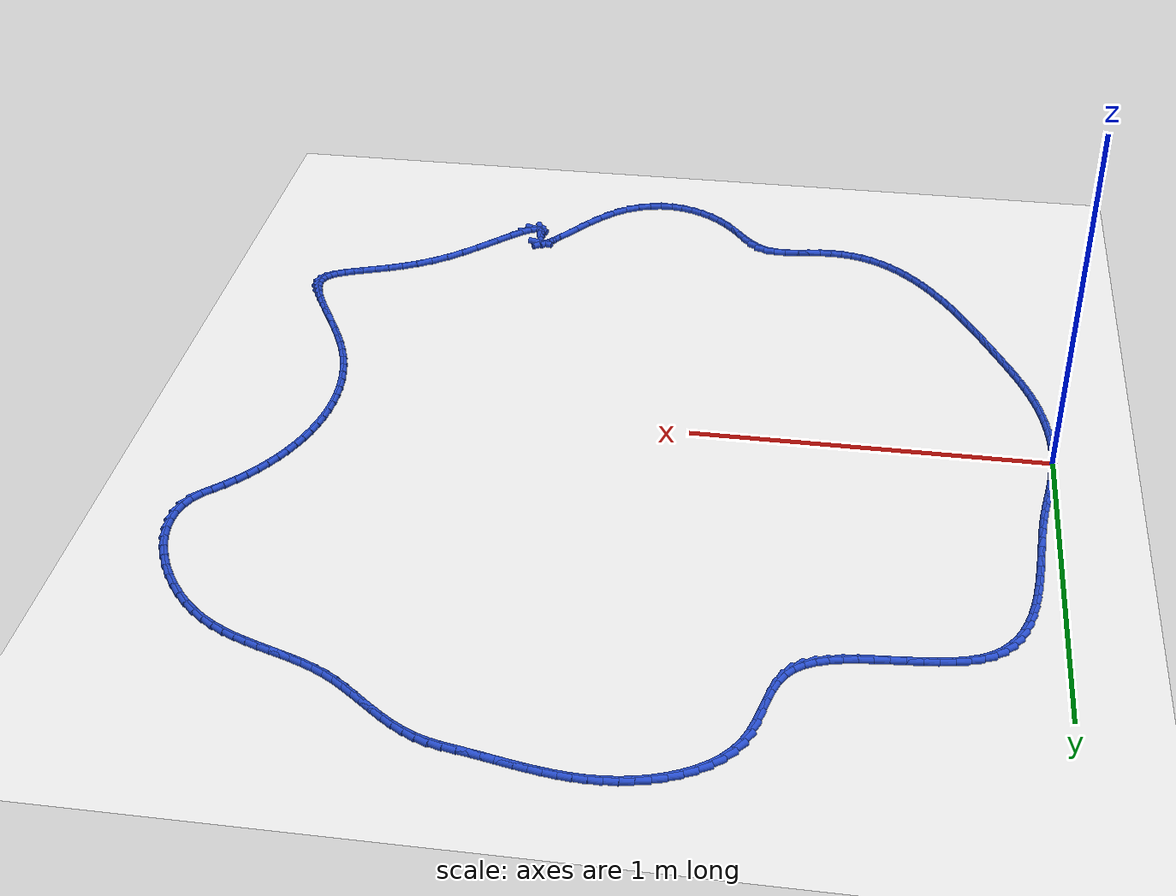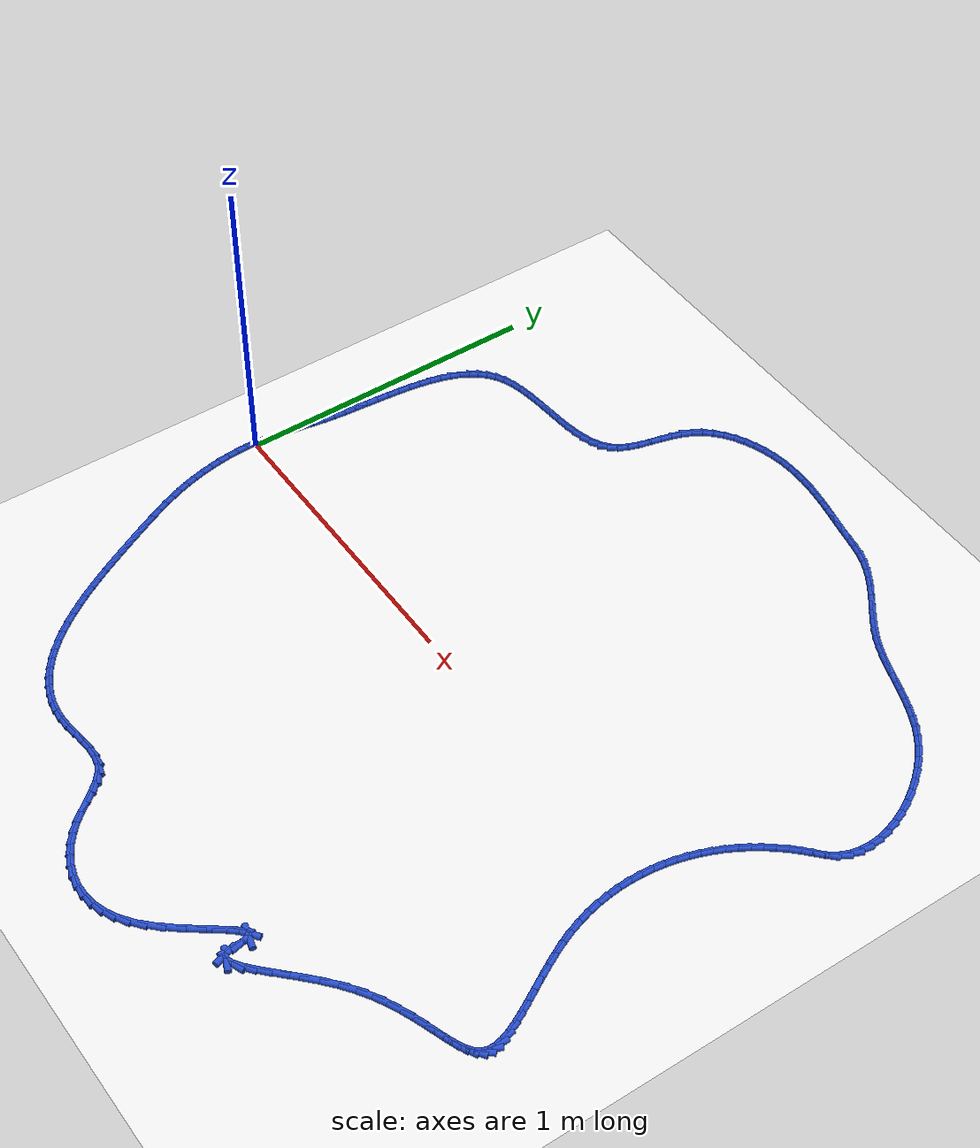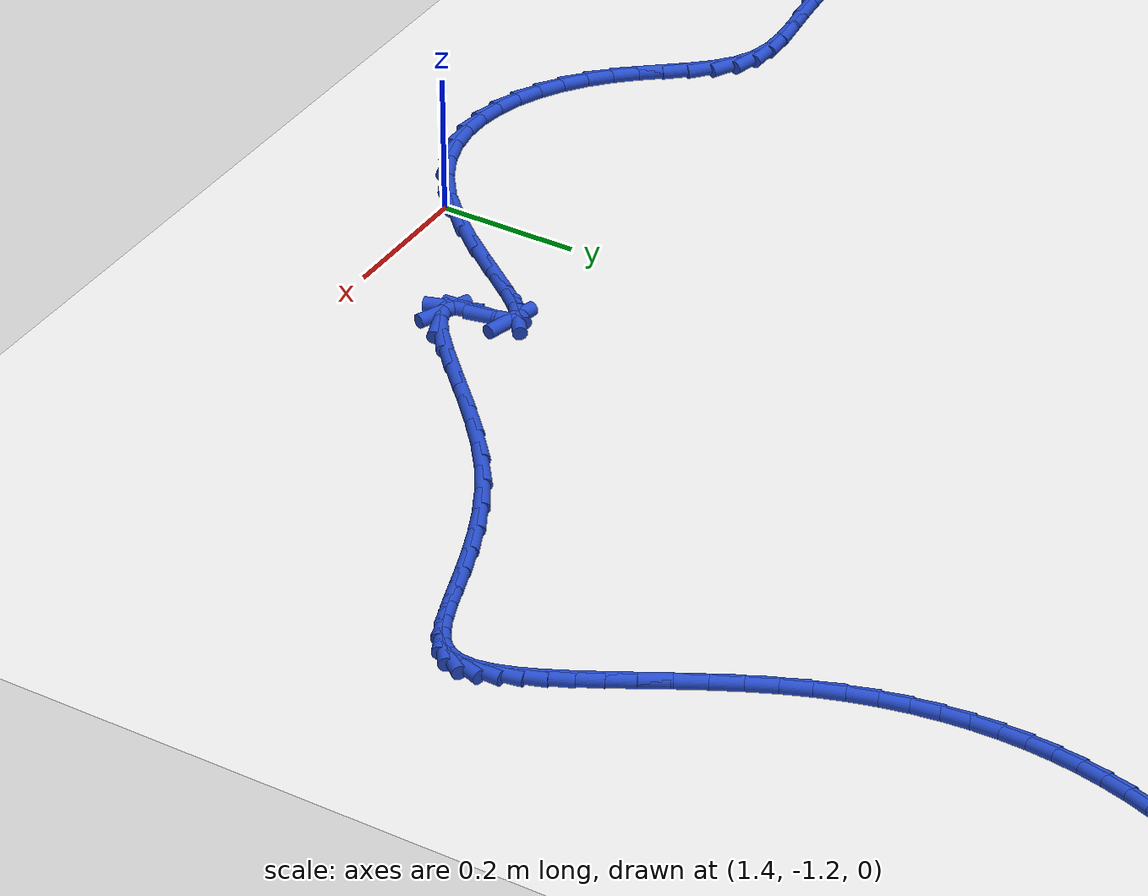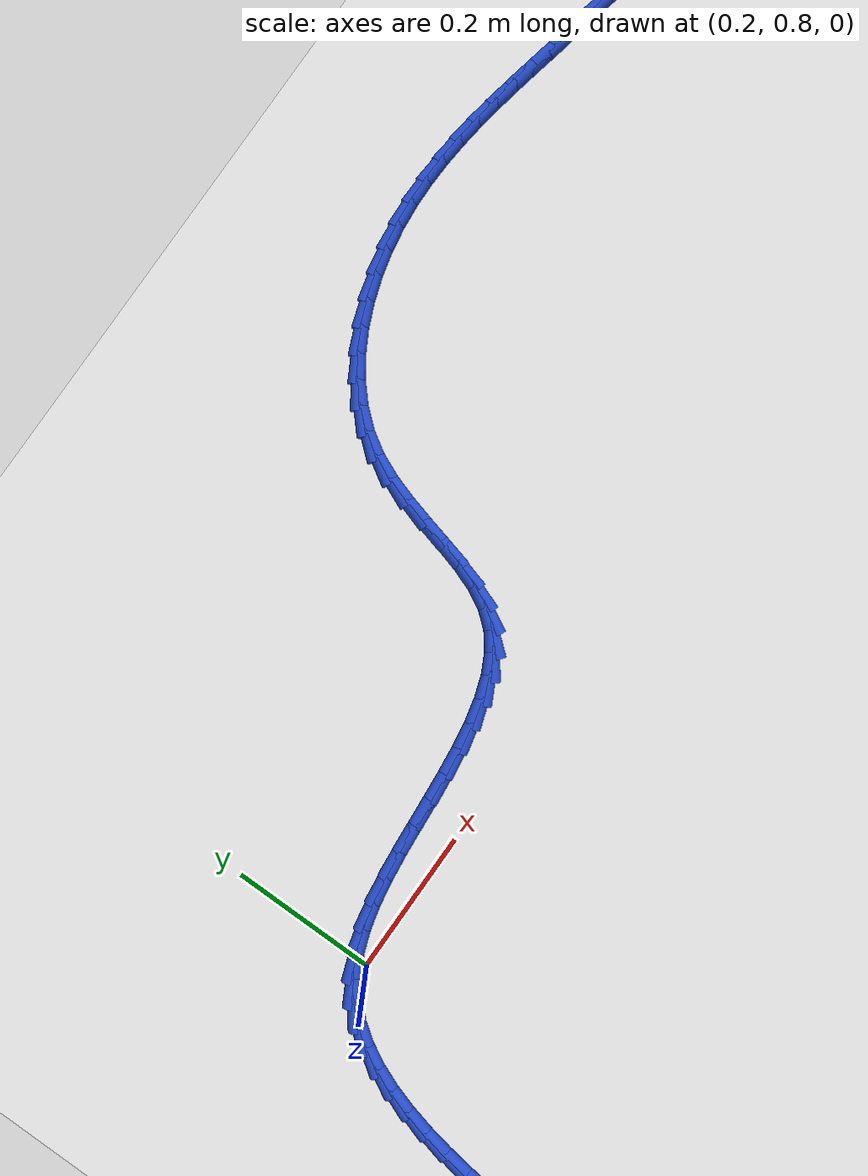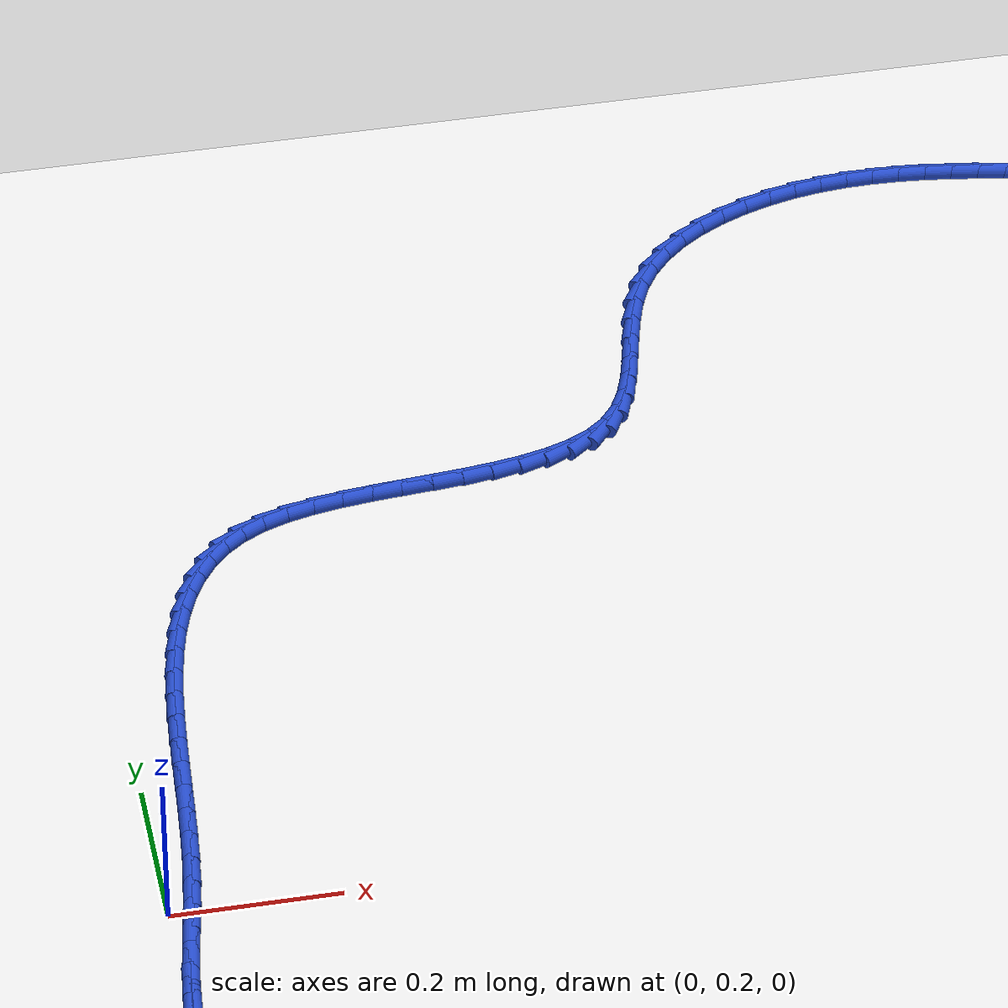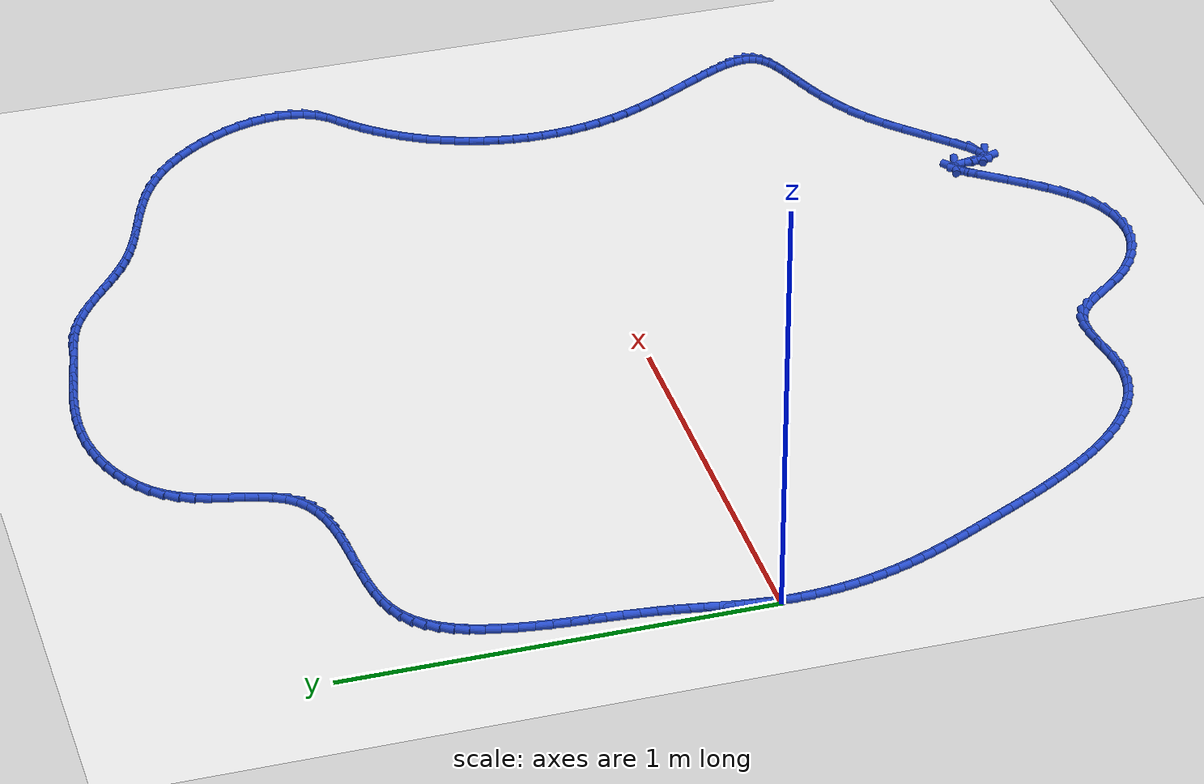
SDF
<sdf version="1.6">
 <world name="default">
  <light name="sun" type="directional">
   <pose>0 0 10 0 -0 0</pose>
   <diffuse>0.8 0.8 0.8 1</diffuse>
   <specular>0.2 0.2 0.2 1</specular>
   <attenuation>
    <range>1000</range>
    <constant>0.9</constant>
    <linear>0.01</linear>
    <quadratic>0.001</quadratic>
   </attenuation>
   <direction>-0.5 0.1 -0.9</direction>
  </light>
  <model name="ground_plane">
   <static>1</static>
   <link name="link">
    <collision name="collision">
     <geometry><plane><normal>0 0 1</normal><size>100 100</size></plane></geometry>
     <surface><friction><ode><mu>100</mu><mu2>50</mu2></ode></friction></surface>
    </collision>
    <visual name="visual">
     <cast_shadows>0</cast_shadows>
     <geometry><plane><normal>0 0 1</normal><size>100 100</size></plane></geometry>
     <material>
      <script><uri>file://media/materials/scripts/gazebo.material</uri><name>Gazebo/WhiteGlow</name></script>
     </material>
    </visual>
   </link>
  </model>
  <gravity>0 0 -9.8</gravity>
  <magnetic_field>6e-06 2.3e-05 -4.2e-05</magnetic_field>
  <atmosphere type="adiabatic"/>
  <physics name="default_physics" default="0" type="ode">
   <max_step_size>0.001</max_step_size>
   <real_time_factor>1</real_time_factor>
   <real_time_update_rate>1000</real_time_update_rate>
  </physics>
  <scene><ambient>0.4 0.4 0.4 1</ambient><background>0.7 0.7 0.7 1</background><shadows>1</shadows></scene>
  <spherical_coordinates>
   <surface_model>EARTH_WGS84</surface_model>
   <latitude_deg>0</latitude_deg>
   <longitude_deg>0</longitude_deg>
   <elevation>0</elevation>
   <heading_deg>0</heading_deg>
  </spherical_coordinates>
  <model name="line">
   <link name="link_0">
    <pose>-1.734723475976807e-17 -6.245004513516506e-17 0.01 0 1.57 1.5053181064349537</pose>
    <collision name="collision">
     <geometry><cylinder><radius>0.01</radius><length>0.08</length></cylinder></geometry>
    </collision>
    <visual name="visual">
     <material>
      <script><name>Gazebo/Blue</name><uri>file://media/materials/scripts/gazebo.material</uri></script>
     </material>
     <geometry><cylinder><radius>0.01</radius><length>0.08</length></cylinder></geometry>
    </visual>
   </link>
   <link name="link_1">
    <pose>0.0021909447616134535 0.03341283107584024 0.01 0 1.57 1.4635662147080735</pose>
    <collision name="collision">
     <geometry><cylinder><radius>0.01</radius><length>0.08</length></cylinder></geometry>
    </collision>
    <visual name="visual">
     <material>
      <script><name>Gazebo/Blue</name><uri>file://media/materials/scripts/gazebo.material</uri></script>
     </material>
     <geometry><cylinder><radius>0.01</radius><length>0.08</length></cylinder></geometry>
    </visual>
   </link>
   <link name="link_2">
    <pose>0.005755805332917543 0.06653027114891552 0.01 0 1.57 1.4323433520758704</pose>
    <collision name="collision">
     <geometry><cylinder><radius>0.01</radius><length>0.08</length></cylinder></geometry>
    </collision>
    <visual name="visual">
     <material>
      <script><name>Gazebo/Blue</name><uri>file://media/materials/scripts/gazebo.material</uri></script>
     </material>
     <geometry><cylinder><radius>0.01</radius><length>0.08</length></cylinder></geometry>
    </visual>
   </link>
   <link name="link_3">
    <pose>0.01036091575959313 0.09957865667562317 0.01 0 1.57 1.4121766671037692</pose>
    <collision name="collision">
     <geometry><cylinder><radius>0.01</radius><length>0.08</length></cylinder></geometry>
    </collision>
    <visual name="visual">
     <material>
      <script><name>Gazebo/Blue</name><uri>file://media/materials/scripts/gazebo.material</uri></script>
     </material>
     <geometry><cylinder><radius>0.01</radius><length>0.08</length></cylinder></geometry>
    </visual>
   </link>
   <link name="link_4">
    <pose>0.015672610087321067 0.13278432411236057 0.01 0 1.57 1.4031460281855865</pose>
    <collision name="collision">
     <geometry><cylinder><radius>0.01</radius><length>0.08</length></cylinder></geometry>
    </collision>
    <visual name="visual">
     <material>
      <script><name>Gazebo/Blue</name><uri>file://media/materials/scripts/gazebo.material</uri></script>
     </material>
     <geometry><cylinder><radius>0.01</radius><length>0.08</length></cylinder></geometry>
    </visual>
   </link>
   <link name="link_5">
    <pose>0.021357222361782245 0.16637360991552522 0.01 0 1.57 1.404965184819467</pose>
    <collision name="collision">
     <geometry><cylinder><radius>0.01</radius><length>0.08</length></cylinder></geometry>
    </collision>
    <visual name="visual">
     <material>
      <script><name>Gazebo/Blue</name><uri>file://media/materials/scripts/gazebo.material</uri></script>
     </material>
     <geometry><cylinder><radius>0.01</radius><length>0.08</length></cylinder></geometry>
    </visual>
   </link>
   <link name="link_6">
    <pose>0.02708108662865752 0.2005728505415144 0.01 0 1.57 1.4170494922797532</pose>
    <collision name="collision">
     <geometry><cylinder><radius>0.01</radius><length>0.08</length></cylinder></geometry>
    </collision>
    <visual name="visual">
     <material>
      <script><name>Gazebo/Blue</name><uri>file://media/materials/scripts/gazebo.material</uri></script>
     </material>
     <geometry><cylinder><radius>0.01</radius><length>0.08</length></cylinder></geometry>
    </visual>
   </link>
   <link name="link_7">
    <pose>0.03251053693362776 0.23560838244672558 0.01 0 1.57 1.438563299679691</pose>
    <collision name="collision">
     <geometry><cylinder><radius>0.01</radius><length>0.08</length></cylinder></geometry>
    </collision>
    <visual name="visual">
     <material>
      <script><name>Gazebo/Blue</name><uri>file://media/materials/scripts/gazebo.material</uri></script>
     </material>
     <geometry><cylinder><radius>0.01</radius><length>0.08</length></cylinder></geometry>
    </visual>
   </link>
   <link name="link_8">
    <pose>0.03731192184006514 0.2717065293652066 0.01 0 1.57 1.4649946939506238</pose>
    <collision name="collision">
     <geometry><cylinder><radius>0.01</radius><length>0.08</length></cylinder></geometry>
    </collision>
    <visual name="visual">
     <material>
      <script><name>Gazebo/Blue</name><uri>file://media/materials/scripts/gazebo.material</uri></script>
     </material>
     <geometry><cylinder><radius>0.01</radius><length>0.08</length></cylinder></geometry>
    </visual>
   </link>
   <link name="link_9">
    <pose>0.041271228462894084 0.30898877167495264 0.01 0 1.57 1.4843571136594005</pose>
    <collision name="collision">
     <geometry><cylinder><radius>0.01</radius><length>0.08</length></cylinder></geometry>
    </collision>
    <visual name="visual">
     <material>
      <script><name>Gazebo/Blue</name><uri>file://media/materials/scripts/gazebo.material</uri></script>
     </material>
     <geometry><cylinder><radius>0.01</radius><length>0.08</length></cylinder></geometry>
    </visual>
   </link>
   <link name="link_10">
    <pose>0.044583962917615336 0.347217714242423 0.01 0 1.57 1.4950510731282154</pose>
    <collision name="collision">
     <geometry><cylinder><radius>0.01</radius><length>0.08</length></cylinder></geometry>
    </collision>
    <visual name="visual">
     <material>
      <script><name>Gazebo/Blue</name><uri>file://media/materials/scripts/gazebo.material</uri></script>
     </material>
     <geometry><cylinder><radius>0.01</radius><length>0.08</length></cylinder></geometry>
    </visual>
   </link>
   <link name="link_11">
    <pose>0.04753318134204573 0.3860792388540751 0.01 0 1.57 1.4977067613809483</pose>
    <collision name="collision">
     <geometry><cylinder><radius>0.01</radius><length>0.08</length></cylinder></geometry>
    </collision>
    <visual name="visual">
     <material>
      <script><name>Gazebo/Blue</name><uri>file://media/materials/scripts/gazebo.material</uri></script>
     </material>
     <geometry><cylinder><radius>0.01</radius><length>0.08</length></cylinder></geometry>
    </visual>
   </link>
   <link name="link_12">
    <pose>0.05040193987400204 0.4252592272963661 0.01 0 1.57 1.4925740464998956</pose>
    <collision name="collision">
     <geometry><cylinder><radius>0.01</radius><length>0.08</length></cylinder></geometry>
    </collision>
    <visual name="visual">
     <material>
      <script><name>Gazebo/Blue</name><uri>file://media/materials/scripts/gazebo.material</uri></script>
     </material>
     <geometry><cylinder><radius>0.01</radius><length>0.08</length></cylinder></geometry>
    </visual>
   </link>
   <link name="link_13">
    <pose>0.05347329465130108 0.4644435613557532 0.01 0 1.57 1.479550793407288</pose>
    <collision name="collision">
     <geometry><cylinder><radius>0.01</radius><length>0.08</length></cylinder></geometry>
    </collision>
    <visual name="visual">
     <material>
      <script><name>Gazebo/Blue</name><uri>file://media/materials/scripts/gazebo.material</uri></script>
     </material>
     <geometry><cylinder><radius>0.01</radius><length>0.08</length></cylinder></geometry>
    </visual>
   </link>
   <link name="link_14">
    <pose>0.05703030181175968 0.5033181228186937 0.01 0 1.57 1.4581861358759884</pose>
    <collision name="collision">
     <geometry><cylinder><radius>0.01</radius><length>0.08</length></cylinder></geometry>
    </collision>
    <visual name="visual">
     <material>
      <script><name>Gazebo/Blue</name><uri>file://media/materials/scripts/gazebo.material</uri></script>
     </material>
     <geometry><cylinder><radius>0.01</radius><length>0.08</length></cylinder></geometry>
    </visual>
   </link>
   <link name="link_15">
    <pose>0.061356017493194616 0.5415687934716449 0.01 0 1.57 1.4276624286103734</pose>
    <collision name="collision">
     <geometry><cylinder><radius>0.01</radius><length>0.08</length></cylinder></geometry>
    </collision>
    <visual name="visual">
     <material>
      <script><name>Gazebo/Blue</name><uri>file://media/materials/scripts/gazebo.material</uri></script>
     </material>
     <geometry><cylinder><radius>0.01</radius><length>0.08</length></cylinder></geometry>
    </visual>
   </link>
   <link name="link_16">
    <pose>0.06673349783342274 0.5788814551010637 0.01 0 1.57 1.3867626916005327</pose>
    <collision name="collision">
     <geometry><cylinder><radius>0.01</radius><length>0.08</length></cylinder></geometry>
    </collision>
    <visual name="visual">
     <material>
      <script><name>Gazebo/Blue</name><uri>file://media/materials/scripts/gazebo.material</uri></script>
     </material>
     <geometry><cylinder><radius>0.01</radius><length>0.08</length></cylinder></geometry>
    </visual>
   </link>
   <link name="link_17">
    <pose>0.07344579897026081 0.6149419894934077 0.01 0 1.57 1.333838802848029</pose>
    <collision name="collision">
     <geometry><cylinder><radius>0.01</radius><length>0.08</length></cylinder></geometry>
    </collision>
    <visual name="visual">
     <material>
      <script><name>Gazebo/Blue</name><uri>file://media/materials/scripts/gazebo.material</uri></script>
     </material>
     <geometry><cylinder><radius>0.01</radius><length>0.08</length></cylinder></geometry>
    </visual>
   </link>
   <link name="link_18">
    <pose>0.0817759770415257 0.649436278435134 0.01 0 1.57 1.266815166307807</pose>
    <collision name="collision">
     <geometry><cylinder><radius>0.01</radius><length>0.08</length></cylinder></geometry>
    </collision>
    <visual name="visual">
     <material>
      <script><name>Gazebo/Blue</name><uri>file://media/materials/scripts/gazebo.material</uri></script>
     </material>
     <geometry><cylinder><radius>0.01</radius><length>0.08</length></cylinder></geometry>
    </visual>
   </link>
   <link name="link_19">
    <pose>0.09200708818503411 0.6820502037126998 0.01 0 1.57 1.1833006721139656</pose>
    <collision name="collision">
     <geometry><cylinder><radius>0.01</radius><length>0.08</length></cylinder></geometry>
    </collision>
    <visual name="visual">
     <material>
      <script><name>Gazebo/Blue</name><uri>file://media/materials/scripts/gazebo.material</uri></script>
     </material>
     <geometry><cylinder><radius>0.01</radius><length>0.08</length></cylinder></geometry>
    </visual>
   </link>
   <link name="link_20">
    <pose>0.104422188538603 0.7124696471125621 0.01 0 1.57 1.080940467783973</pose>
    <collision name="collision">
     <geometry><cylinder><radius>0.01</radius><length>0.08</length></cylinder></geometry>
    </collision>
    <visual name="visual">
     <material>
      <script><name>Gazebo/Blue</name><uri>file://media/materials/scripts/gazebo.material</uri></script>
     </material>
     <geometry><cylinder><radius>0.01</radius><length>0.08</length></cylinder></geometry>
    </visual>
   </link>
   <link name="link_21">
    <pose>0.11930433424004905 0.7403804904211786 0.01 0 1.57 0.9581852893349911</pose>
    <collision name="collision">
     <geometry><cylinder><radius>0.01</radius><length>0.08</length></cylinder></geometry>
    </collision>
    <visual name="visual">
     <material>
      <script><name>Gazebo/Blue</name><uri>file://media/materials/scripts/gazebo.material</uri></script>
     </material>
     <geometry><cylinder><radius>0.01</radius><length>0.08</length></cylinder></geometry>
    </visual>
   </link>
   <link name="link_22">
    <pose>0.13693658142718912 0.7654686154250061 0.01 0 1.57 0.815562250640637</pose>
    <collision name="collision">
     <geometry><cylinder><radius>0.01</radius><length>0.08</length></cylinder></geometry>
    </collision>
    <visual name="visual">
     <material>
      <script><name>Gazebo/Blue</name><uri>file://media/materials/scripts/gazebo.material</uri></script>
     </material>
     <geometry><cylinder><radius>0.01</radius><length>0.08</length></cylinder></geometry>
    </visual>
   </link>
   <link name="link_23">
    <pose>0.15760198623783994 0.7874199039105019 0.01 0 1.57 0.6570808959312375</pose>
    <collision name="collision">
     <geometry><cylinder><radius>0.01</radius><length>0.08</length></cylinder></geometry>
    </collision>
    <visual name="visual">
     <material>
      <script><name>Gazebo/Blue</name><uri>file://media/materials/scripts/gazebo.material</uri></script>
     </material>
     <geometry><cylinder><radius>0.01</radius><length>0.08</length></cylinder></geometry>
    </visual>
   </link>
   <link name="link_24">
    <pose>0.18158360480981847 0.8059202376641235 0.01 0 1.57 0.4918538268782702</pose>
    <collision name="collision">
     <geometry><cylinder><radius>0.01</radius><length>0.08</length></cylinder></geometry>
    </collision>
    <visual name="visual">
     <material>
      <script><name>Gazebo/Blue</name><uri>file://media/materials/scripts/gazebo.material</uri></script>
     </material>
     <geometry><cylinder><radius>0.01</radius><length>0.08</length></cylinder></geometry>
    </visual>
   </link>
   <link name="link_25">
    <pose>0.20913826373428557 0.8206832455608908 0.01 0 1.57 0.3483219362038101</pose>
    <collision name="collision">
     <geometry><cylinder><radius>0.01</radius><length>0.08</length></cylinder></geometry>
    </collision>
    <visual name="visual">
     <material>
      <script><name>Gazebo/Blue</name><uri>file://media/materials/scripts/gazebo.material</uri></script>
     </material>
     <geometry><cylinder><radius>0.01</radius><length>0.08</length></cylinder></geometry>
    </visual>
   </link>
   <link name="link_26">
    <pose>0.240060230521404 0.8319118774676965 0.01 0 1.57 0.2420111601027854</pose>
    <collision name="collision">
     <geometry><cylinder><radius>0.01</radius><length>0.08</length></cylinder></geometry>
    </collision>
    <visual name="visual">
     <material>
      <script><name>Gazebo/Blue</name><uri>file://media/materials/scripts/gazebo.material</uri></script>
     </material>
     <geometry><cylinder><radius>0.01</radius><length>0.08</length></cylinder></geometry>
    </visual>
   </link>
   <link name="link_27">
    <pose>0.27374805530892843 0.8402276953274301 0.01 0 1.57 0.16690782609652852</pose>
    <collision name="collision">
     <geometry><cylinder><radius>0.01</radius><length>0.08</length></cylinder></geometry>
    </collision>
    <visual name="visual">
     <material>
      <script><name>Gazebo/Blue</name><uri>file://media/materials/scripts/gazebo.material</uri></script>
     </material>
     <geometry><cylinder><radius>0.01</radius><length>0.08</length></cylinder></geometry>
    </visual>
   </link>
   <link name="link_28">
    <pose>0.30958752919378213 0.8462657583134355 0.01 0 1.57 0.11705816339653283</pose>
    <collision name="collision">
     <geometry><cylinder><radius>0.01</radius><length>0.08</length></cylinder></geometry>
    </collision>
    <visual name="visual">
     <material>
      <script><name>Gazebo/Blue</name><uri>file://media/materials/scripts/gazebo.material</uri></script>
     </material>
     <geometry><cylinder><radius>0.01</radius><length>0.08</length></cylinder></geometry>
    </visual>
   </link>
   <link name="link_29">
    <pose>0.346964443272888 0.8506611255990569 0.01 0 1.57 0.08822256442507632</pose>
    <collision name="collision">
     <geometry><cylinder><radius>0.01</radius><length>0.08</length></cylinder></geometry>
    </collision>
    <visual name="visual">
     <material>
      <script><name>Gazebo/Blue</name><uri>file://media/materials/scripts/gazebo.material</uri></script>
     </material>
     <geometry><cylinder><radius>0.01</radius><length>0.08</length></cylinder></geometry>
    </visual>
   </link>
   <link name="link_30">
    <pose>0.38526458864316976 0.8540488563576387 0.01 0 1.57 0.07793605500294389</pose>
    <collision name="collision">
     <geometry><cylinder><radius>0.01</radius><length>0.08</length></cylinder></geometry>
    </collision>
    <visual name="visual">
     <material>
      <script><name>Gazebo/Blue</name><uri>file://media/materials/scripts/gazebo.material</uri></script>
     </material>
     <geometry><cylinder><radius>0.01</radius><length>0.08</length></cylinder></geometry>
    </visual>
   </link>
   <link name="link_31">
    <pose>0.42387375640155023 0.8570640097625246 0.01 0 1.57 0.0853611138401619</pose>
    <collision name="collision">
     <geometry><cylinder><radius>0.01</radius><length>0.08</length></cylinder></geometry>
    </collision>
    <visual name="visual">
     <material>
      <script><name>Gazebo/Blue</name><uri>file://media/materials/scripts/gazebo.material</uri></script>
     </material>
     <geometry><cylinder><radius>0.01</radius><length>0.08</length></cylinder></geometry>
    </visual>
   </link>
   <link name="link_32">
    <pose>0.4621777376449526 0.8603416449870586 0.01 0 1.57 0.11122087228293132</pose>
    <collision name="collision">
     <geometry><cylinder><radius>0.01</radius><length>0.08</length></cylinder></geometry>
    </collision>
    <visual name="visual">
     <material>
      <script><name>Gazebo/Blue</name><uri>file://media/materials/scripts/gazebo.material</uri></script>
     </material>
     <geometry><cylinder><radius>0.01</radius><length>0.08</length></cylinder></geometry>
    </visual>
   </link>
   <link name="link_33">
    <pose>0.49956232347030005 0.864516821204585 0.01 0 1.57 0.15788329839241244</pose>
    <collision name="collision">
     <geometry><cylinder><radius>0.01</radius><length>0.08</length></cylinder></geometry>
    </collision>
    <visual name="visual">
     <material>
      <script><name>Gazebo/Blue</name><uri>file://media/materials/scripts/gazebo.material</uri></script>
     </material>
     <geometry><cylinder><radius>0.01</radius><length>0.08</length></cylinder></geometry>
    </visual>
   </link>
   <link name="link_34">
    <pose>0.5354133049745157 0.8702245975884476 0.01 0 1.57 0.22955165410758305</pose>
    <collision name="collision">
     <geometry><cylinder><radius>0.01</radius><length>0.08</length></cylinder></geometry>
    </collision>
    <visual name="visual">
     <material>
      <script><name>Gazebo/Blue</name><uri>file://media/materials/scripts/gazebo.material</uri></script>
     </material>
     <geometry><cylinder><radius>0.01</radius><length>0.08</length></cylinder></geometry>
    </visual>
   </link>
   <link name="link_35">
    <pose>0.569116473254523 0.8781000333119909 0.01 0 1.57 0.33231344397236207</pose>
    <collision name="collision">
     <geometry><cylinder><radius>0.01</radius><length>0.08</length></cylinder></geometry>
    </collision>
    <visual name="visual">
     <material>
      <script><name>Gazebo/Blue</name><uri>file://media/materials/scripts/gazebo.material</uri></script>
     </material>
     <geometry><cylinder><radius>0.01</radius><length>0.08</length></cylinder></geometry>
    </visual>
   </link>
   <link name="link_36">
    <pose>0.6000576194072447 0.8887781875485583 0.01 0 1.57 0.4732789290980361</pose>
    <collision name="collision">
     <geometry><cylinder><radius>0.01</radius><length>0.08</length></cylinder></geometry>
    </collision>
    <visual name="visual">
     <material>
      <script><name>Gazebo/Blue</name><uri>file://media/materials/scripts/gazebo.material</uri></script>
     </material>
     <geometry><cylinder><radius>0.01</radius><length>0.08</length></cylinder></geometry>
    </visual>
   </link>
   <link name="link_37">
    <pose>0.627622534529604 0.9028941194714943 0.01 0 1.57 0.6571479314906479</pose>
    <collision name="collision">
     <geometry><cylinder><radius>0.01</radius><length>0.08</length></cylinder></geometry>
    </collision>
    <visual name="visual">
     <material>
      <script><name>Gazebo/Blue</name><uri>file://media/materials/scripts/gazebo.material</uri></script>
     </material>
     <geometry><cylinder><radius>0.01</radius><length>0.08</length></cylinder></geometry>
    </visual>
   </link>
   <link name="link_38">
    <pose>0.6511970097185245 0.9210828882541429 0.01 0 1.57 0.8780879587779196</pose>
    <collision name="collision">
     <geometry><cylinder><radius>0.01</radius><length>0.08</length></cylinder></geometry>
    </collision>
    <visual name="visual">
     <material>
      <script><name>Gazebo/Blue</name><uri>file://media/materials/scripts/gazebo.material</uri></script>
     </material>
     <geometry><cylinder><radius>0.01</radius><length>0.08</length></cylinder></geometry>
    </visual>
   </link>
   <link name="link_39">
    <pose>0.670185007129371 0.9439627620193984 0.01 0 1.57 1.0833853122143733</pose>
    <collision name="collision">
     <geometry><cylinder><radius>0.01</radius><length>0.08</length></cylinder></geometry>
    </collision>
    <visual name="visual">
     <material>
      <script><name>Gazebo/Blue</name><uri>file://media/materials/scripts/gazebo.material</uri></script>
     </material>
     <geometry><cylinder><radius>0.01</radius><length>0.08</length></cylinder></geometry>
    </visual>
   </link>
   <link name="link_40">
    <pose>0.6847534799290174 0.9714469635232001 0.01 0 1.57 1.2206443785357857</pose>
    <collision name="collision">
     <geometry><cylinder><radius>0.01</radius><length>0.08</length></cylinder></geometry>
    </collision>
    <visual name="visual">
     <material>
      <script><name>Gazebo/Blue</name><uri>file://media/materials/scripts/gazebo.material</uri></script>
     </material>
     <geometry><cylinder><radius>0.01</radius><length>0.08</length></cylinder></geometry>
    </visual>
   </link>
   <link name="link_41">
    <pose>0.6960945747997966 1.0025013807201573 0.01 0 1.57 1.2980307831445093</pose>
    <collision name="collision">
     <geometry><cylinder><radius>0.01</radius><length>0.08</length></cylinder></geometry>
    </collision>
    <visual name="visual">
     <material>
      <script><name>Gazebo/Blue</name><uri>file://media/materials/scripts/gazebo.material</uri></script>
     </material>
     <geometry><cylinder><radius>0.01</radius><length>0.08</length></cylinder></geometry>
    </visual>
   </link>
   <link name="link_42">
    <pose>0.7054724885665461 1.0360253232980372 0.01 0 1.57 1.327011994624476</pose>
    <collision name="collision">
     <geometry><cylinder><radius>0.01</radius><length>0.08</length></cylinder></geometry>
    </collision>
    <visual name="visual">
     <material>
      <script><name>Gazebo/Blue</name><uri>file://media/materials/scripts/gazebo.material</uri></script>
     </material>
     <geometry><cylinder><radius>0.01</radius><length>0.08</length></cylinder></geometry>
    </visual>
   </link>
   <link name="link_43">
    <pose>0.7141514180541033 1.0709181009446078 0.01 0 1.57 1.3137048929895958</pose>
    <collision name="collision">
     <geometry><cylinder><radius>0.01</radius><length>0.08</length></cylinder></geometry>
    </collision>
    <visual name="visual">
     <material>
      <script><name>Gazebo/Blue</name><uri>file://media/materials/scripts/gazebo.material</uri></script>
     </material>
     <geometry><cylinder><radius>0.01</radius><length>0.08</length></cylinder></geometry>
    </visual>
   </link>
   <link name="link_44">
    <pose>0.7233955600873057 1.1060790233476363 0.01 0 1.57 1.2587573330821908</pose>
    <collision name="collision">
     <geometry><cylinder><radius>0.01</radius><length>0.08</length></cylinder></geometry>
    </collision>
    <visual name="visual">
     <material>
      <script><name>Gazebo/Blue</name><uri>file://media/materials/scripts/gazebo.material</uri></script>
     </material>
     <geometry><cylinder><radius>0.01</radius><length>0.08</length></cylinder></geometry>
    </visual>
   </link>
   <link name="link_45">
    <pose>0.7344691114909911 1.1404074001948907 0.01 0 1.57 1.1585340089251464</pose>
    <collision name="collision">
     <geometry><cylinder><radius>0.01</radius><length>0.08</length></cylinder></geometry>
    </collision>
    <visual name="visual">
     <material>
      <script><name>Gazebo/Blue</name><uri>file://media/materials/scripts/gazebo.material</uri></script>
     </material>
     <geometry><cylinder><radius>0.01</radius><length>0.08</length></cylinder></geometry>
    </visual>
   </link>
   <link name="link_46">
    <pose>0.7486362690899965 1.1728025411741387 0.01 0 1.57 1.0141743789651938</pose>
    <collision name="collision">
     <geometry><cylinder><radius>0.01</radius><length>0.08</length></cylinder></geometry>
    </collision>
    <visual name="visual">
     <material>
      <script><name>Gazebo/Blue</name><uri>file://media/materials/scripts/gazebo.material</uri></script>
     </material>
     <geometry><cylinder><radius>0.01</radius><length>0.08</length></cylinder></geometry>
    </visual>
   </link>
   <link name="link_47">
    <pose>0.7669785465220736 1.202279714184704 0.01 0 1.57 0.8652497493111576</pose>
    <collision name="collision">
     <geometry><cylinder><radius>0.01</radius><length>0.08</length></cylinder></geometry>
    </collision>
    <visual name="visual">
     <material>
      <script><name>Gazebo/Blue</name><uri>file://media/materials/scripts/gazebo.material</uri></script>
     </material>
     <geometry><cylinder><radius>0.01</radius><length>0.08</length></cylinder></geometry>
    </visual>
   </link>
   <link name="link_48">
    <pose>0.7893999314316502 1.2286016221275904 0.01 0 1.57 0.7302988509410004</pose>
    <collision name="collision">
     <geometry><cylinder><radius>0.01</radius><length>0.08</length></cylinder></geometry>
    </collision>
    <visual name="visual">
     <material>
      <script><name>Gazebo/Blue</name><uri>file://media/materials/scripts/gazebo.material</uri></script>
     </material>
     <geometry><cylinder><radius>0.01</radius><length>0.08</length></cylinder></geometry>
    </visual>
   </link>
   <link name="link_49">
    <pose>0.815337349708645 1.251827435502178 0.01 0 1.57 0.6099634138188034</pose>
    <collision name="collision">
     <geometry><cylinder><radius>0.01</radius><length>0.08</length></cylinder></geometry>
    </collision>
    <visual name="visual">
     <material>
      <script><name>Gazebo/Blue</name><uri>file://media/materials/scripts/gazebo.material</uri></script>
     </material>
     <geometry><cylinder><radius>0.01</radius><length>0.08</length></cylinder></geometry>
    </visual>
   </link>
   <link name="link_50">
    <pose>0.844226552078059 1.2720170707441545 0.01 0 1.57 0.503117314271276</pose>
    <collision name="collision">
     <geometry><cylinder><radius>0.01</radius><length>0.08</length></cylinder></geometry>
    </collision>
    <visual name="visual">
     <material>
      <script><name>Gazebo/Blue</name><uri>file://media/materials/scripts/gazebo.material</uri></script>
     </material>
     <geometry><cylinder><radius>0.01</radius><length>0.08</length></cylinder></geometry>
    </visual>
   </link>
   <link name="link_51">
    <pose>0.8755032892648935 1.2892304442892093 0.01 0 1.57 0.40772919543496045</pose>
    <collision name="collision">
     <geometry><cylinder><radius>0.01</radius><length>0.08</length></cylinder></geometry>
    </collision>
    <visual name="visual">
     <material>
      <script><name>Gazebo/Blue</name><uri>file://media/materials/scripts/gazebo.material</uri></script>
     </material>
     <geometry><cylinder><radius>0.01</radius><length>0.08</length></cylinder></geometry>
    </visual>
   </link>
   <link name="link_52">
    <pose>0.9086033119941495 1.3035274725730297 0.01 0 1.57 0.3214251846444933</pose>
    <collision name="collision">
     <geometry><cylinder><radius>0.01</radius><length>0.08</length></cylinder></geometry>
    </collision>
    <visual name="visual">
     <material>
      <script><name>Gazebo/Blue</name><uri>file://media/materials/scripts/gazebo.material</uri></script>
     </material>
     <geometry><cylinder><radius>0.01</radius><length>0.08</length></cylinder></geometry>
    </visual>
   </link>
   <link name="link_53">
    <pose>0.9429623709908274 1.3149680720313042 0.01 0 1.57 0.24177096613294172</pose>
    <collision name="collision">
     <geometry><cylinder><radius>0.01</radius><length>0.08</length></cylinder></geometry>
    </collision>
    <visual name="visual">
     <material>
      <script><name>Gazebo/Blue</name><uri>file://media/materials/scripts/gazebo.material</uri></script>
     </material>
     <geometry><cylinder><radius>0.01</radius><length>0.08</length></cylinder></geometry>
    </visual>
   </link>
   <link name="link_54">
    <pose>0.9780162169799287 1.3236121590997212 0.01 0 1.57 0.1663503867294449</pose>
    <collision name="collision">
     <geometry><cylinder><radius>0.01</radius><length>0.08</length></cylinder></geometry>
    </collision>
    <visual name="visual">
     <material>
      <script><name>Gazebo/Blue</name><uri>file://media/materials/scripts/gazebo.material</uri></script>
     </material>
     <geometry><cylinder><radius>0.01</radius><length>0.08</length></cylinder></geometry>
    </visual>
   </link>
   <link name="link_55">
    <pose>1.0132007655844522 1.3295197153487555 0.01 0 1.57 0.09392492605285885</pose>
    <collision name="collision">
     <geometry><cylinder><radius>0.01</radius><length>0.08</length></cylinder></geometry>
    </collision>
    <visual name="visual">
     <material>
      <script><name>Gazebo/Blue</name><uri>file://media/materials/scripts/gazebo.material</uri></script>
     </material>
     <geometry><cylinder><radius>0.01</radius><length>0.08</length></cylinder></geometry>
    </visual>
   </link>
   <link name="link_56">
    <pose>1.0480936419303888 1.3328066976695312 0.01 0 1.57 0.027191372931767228</pose>
    <collision name="collision">
     <geometry><cylinder><radius>0.01</radius><length>0.08</length></cylinder></geometry>
    </collision>
    <visual name="visual">
     <material>
      <script><name>Gazebo/Blue</name><uri>file://media/materials/scripts/gazebo.material</uri></script>
     </material>
     <geometry><cylinder><radius>0.01</radius><length>0.08</length></cylinder></geometry>
    </visual>
   </link>
   <link name="link_57">
    <pose>1.0826727761082229 1.3337471836033115 0.01 0 1.57 -0.03216895014261414</pose>
    <collision name="collision">
     <geometry><cylinder><radius>0.01</radius><length>0.08</length></cylinder></geometry>
    </collision>
    <visual name="visual">
     <material>
      <script><name>Gazebo/Blue</name><uri>file://media/materials/scripts/gazebo.material</uri></script>
     </material>
     <geometry><cylinder><radius>0.01</radius><length>0.08</length></cylinder></geometry>
    </visual>
   </link>
   <link name="link_58">
    <pose>1.1169862817668372 1.3326429732300953 0.01 0 1.57 -0.08330940805954572</pose>
    <collision name="collision">
     <geometry><cylinder><radius>0.01</radius><length>0.08</length></cylinder></geometry>
    </collision>
    <visual name="visual">
     <material>
      <script><name>Gazebo/Blue</name><uri>file://media/materials/scripts/gazebo.material</uri></script>
     </material>
     <geometry><cylinder><radius>0.01</radius><length>0.08</length></cylinder></geometry>
    </visual>
   </link>
   <link name="link_59">
    <pose>1.1510822725551149 1.3297958666298797 0.01 0 1.57 -0.125729789281232</pose>
    <collision name="collision">
     <geometry><cylinder><radius>0.01</radius><length>0.08</length></cylinder></geometry>
    </collision>
    <visual name="visual">
     <material>
      <script><name>Gazebo/Blue</name><uri>file://media/materials/scripts/gazebo.material</uri></script>
     </material>
     <geometry><cylinder><radius>0.01</radius><length>0.08</length></cylinder></geometry>
    </visual>
   </link>
   <link name="link_60">
    <pose>1.185008862121938 1.3255076638826624 0.01 0 1.57 -0.15919314802991205</pose>
    <collision name="collision">
     <geometry><cylinder><radius>0.01</radius><length>0.08</length></cylinder></geometry>
    </collision>
    <visual name="visual">
     <material>
      <script><name>Gazebo/Blue</name><uri>file://media/materials/scripts/gazebo.material</uri></script>
     </material>
     <geometry><cylinder><radius>0.01</radius><length>0.08</length></cylinder></geometry>
    </visual>
   </link>
   <link name="link_61">
    <pose>1.2188141641161887 1.3200801650684408 0.01 0 1.57 -0.18363541465684052</pose>
    <collision name="collision">
     <geometry><cylinder><radius>0.01</radius><length>0.08</length></cylinder></geometry>
    </collision>
    <visual name="visual">
     <material>
      <script><name>Gazebo/Blue</name><uri>file://media/materials/scripts/gazebo.material</uri></script>
     </material>
     <geometry><cylinder><radius>0.01</radius><length>0.08</length></cylinder></geometry>
    </visual>
   </link>
   <link name="link_62">
    <pose>1.2525462921867496 1.3138151702672125 0.01 0 1.57 -0.19908594524107748</pose>
    <collision name="collision">
     <geometry><cylinder><radius>0.01</radius><length>0.08</length></cylinder></geometry>
    </collision>
    <visual name="visual">
     <material>
      <script><name>Gazebo/Blue</name><uri>file://media/materials/scripts/gazebo.material</uri></script>
     </material>
     <geometry><cylinder><radius>0.01</radius><length>0.08</length></cylinder></geometry>
    </visual>
   </link>
   <link name="link_63">
    <pose>1.2862533599825043 1.3070144795589753 0.01 0 1.57 -0.20560785737708023</pose>
    <collision name="collision">
     <geometry><cylinder><radius>0.01</radius><length>0.08</length></cylinder></geometry>
    </collision>
    <visual name="visual">
     <material>
      <script><name>Gazebo/Blue</name><uri>file://media/materials/scripts/gazebo.material</uri></script>
     </material>
     <geometry><cylinder><radius>0.01</radius><length>0.08</length></cylinder></geometry>
    </visual>
   </link>
   <link name="link_64">
    <pose>1.3199834811523343 1.2999798930237267 0.01 0 1.57 -0.2032607247363708</pose>
    <collision name="collision">
     <geometry><cylinder><radius>0.01</radius><length>0.08</length></cylinder></geometry>
    </collision>
    <visual name="visual">
     <material>
      <script><name>Gazebo/Blue</name><uri>file://media/materials/scripts/gazebo.material</uri></script>
     </material>
     <geometry><cylinder><radius>0.01</radius><length>0.08</length></cylinder></geometry>
    </visual>
   </link>
   <link name="link_65">
    <pose>1.3537847693451224 1.2930132107414642 0.01 0 1.57 -0.19248460920277682</pose>
    <collision name="collision">
     <geometry><cylinder><radius>0.01</radius><length>0.08</length></cylinder></geometry>
    </collision>
    <visual name="visual">
     <material>
      <script><name>Gazebo/Blue</name><uri>file://media/materials/scripts/gazebo.material</uri></script>
     </material>
     <geometry><cylinder><radius>0.01</radius><length>0.08</length></cylinder></geometry>
    </visual>
   </link>
   <link name="link_66">
    <pose>1.3877007568035449 1.2864030667996744 0.01 0 1.57 -0.1939090116015446</pose>
    <collision name="collision">
     <geometry><cylinder><radius>0.01</radius><length>0.08</length></cylinder></geometry>
    </collision>
    <visual name="visual">
     <material>
      <script><name>Gazebo/Blue</name><uri>file://media/materials/scripts/gazebo.material</uri></script>
     </material>
     <geometry><cylinder><radius>0.01</radius><length>0.08</length></cylinder></geometry>
    </visual>
   </link>
   <link name="link_67">
    <pose>1.4215383746731576 1.2797581537718576 0.01 0 1.57 -0.23819893880994616</pose>
    <collision name="collision">
     <geometry><cylinder><radius>0.01</radius><length>0.08</length></cylinder></geometry>
    </collision>
    <visual name="visual">
     <material>
      <script><name>Gazebo/Blue</name><uri>file://media/materials/scripts/gazebo.material</uri></script>
     </material>
     <geometry><cylinder><radius>0.01</radius><length>0.08</length></cylinder></geometry>
    </visual>
   </link>
   <link name="link_68">
    <pose>1.454758289191289 1.2716920721173572 0.01 0 1.57 -0.3280379708383834</pose>
    <collision name="collision">
     <geometry><cylinder><radius>0.01</radius><length>0.08</length></cylinder></geometry>
    </collision>
    <visual name="visual">
     <material>
      <script><name>Gazebo/Blue</name><uri>file://media/materials/scripts/gazebo.material</uri></script>
     </material>
     <geometry><cylinder><radius>0.01</radius><length>0.08</length></cylinder></geometry>
    </visual>
   </link>
   <link name="link_69">
    <pose>1.486810810175451 1.2607835057184145 0.01 0 1.57 -0.4318677894783215</pose>
    <collision name="collision">
     <geometry><cylinder><radius>0.01</radius><length>0.08</length></cylinder></geometry>
    </collision>
    <visual name="visual">
     <material>
      <script><name>Gazebo/Blue</name><uri>file://media/materials/scripts/gazebo.material</uri></script>
     </material>
     <geometry><cylinder><radius>0.01</radius><length>0.08</length></cylinder></geometry>
    </visual>
   </link>
   <link name="link_70">
    <pose>1.5175388465289499 1.246621457335257 0.01 0 1.57 -0.5161707550218443</pose>
    <collision name="collision">
     <geometry><cylinder><radius>0.01</radius><length>0.08</length></cylinder></geometry>
    </collision>
    <visual name="visual">
     <material>
      <script><name>Gazebo/Blue</name><uri>file://media/materials/scripts/gazebo.material</uri></script>
     </material>
     <geometry><cylinder><radius>0.01</radius><length>0.08</length></cylinder></geometry>
    </visual>
   </link>
   <link name="link_71">
    <pose>1.5471767560998306 1.2298022888202567 0.01 0 1.57 -0.579225018899423</pose>
    <collision name="collision">
     <geometry><cylinder><radius>0.01</radius><length>0.08</length></cylinder></geometry>
    </collision>
    <visual name="visual">
     <material>
      <script><name>Gazebo/Blue</name><uri>file://media/materials/scripts/gazebo.material</uri></script>
     </material>
     <geometry><cylinder><radius>0.01</radius><length>0.08</length></cylinder></geometry>
    </visual>
   </link>
   <link name="link_72">
    <pose>1.5759758265140758 1.2109659293056565 0.01 0 1.57 -0.6217157622878199</pose>
    <collision name="collision">
     <geometry><cylinder><radius>0.01</radius><length>0.08</length></cylinder></geometry>
    </collision>
    <visual name="visual">
     <material>
      <script><name>Gazebo/Blue</name><uri>file://media/materials/scripts/gazebo.material</uri></script>
     </material>
     <geometry><cylinder><radius>0.01</radius><length>0.08</length></cylinder></geometry>
    </visual>
   </link>
   <link name="link_73">
    <pose>1.6041873453976654 1.1907523079237008 0.01 0 1.57 -0.6445223161636893</pose>
    <collision name="collision">
     <geometry><cylinder><radius>0.01</radius><length>0.08</length></cylinder></geometry>
    </collision>
    <visual name="visual">
     <material>
      <script><name>Gazebo/Blue</name><uri>file://media/materials/scripts/gazebo.material</uri></script>
     </material>
     <geometry><cylinder><radius>0.01</radius><length>0.08</length></cylinder></geometry>
    </visual>
   </link>
   <link name="link_74">
    <pose>1.6320626003765817 1.1698013538066325 0.01 0 1.57 -0.6482203254890119</pose>
    <collision name="collision">
     <geometry><cylinder><radius>0.01</radius><length>0.08</length></cylinder></geometry>
    </collision>
    <visual name="visual">
     <material>
      <script><name>Gazebo/Blue</name><uri>file://media/materials/scripts/gazebo.material</uri></script>
     </material>
     <geometry><cylinder><radius>0.01</radius><length>0.08</length></cylinder></geometry>
    </visual>
   </link>
   <link name="link_75">
    <pose>1.6598528790768055 1.1487529960866965 0.01 0 1.57 -0.6328496119055224</pose>
    <collision name="collision">
     <geometry><cylinder><radius>0.01</radius><length>0.08</length></cylinder></geometry>
    </collision>
    <visual name="visual">
     <material>
      <script><name>Gazebo/Blue</name><uri>file://media/materials/scripts/gazebo.material</uri></script>
     </material>
     <geometry><cylinder><radius>0.01</radius><length>0.08</length></cylinder></geometry>
    </visual>
   </link>
   <link name="link_76">
    <pose>1.6878094691243184 1.1282471638961358 0.01 0 1.57 -0.5978735056712724</pose>
    <collision name="collision">
     <geometry><cylinder><radius>0.01</radius><length>0.08</length></cylinder></geometry>
    </collision>
    <visual name="visual">
     <material>
      <script><name>Gazebo/Blue</name><uri>file://media/materials/scripts/gazebo.material</uri></script>
     </material>
     <geometry><cylinder><radius>0.01</radius><length>0.08</length></cylinder></geometry>
    </visual>
   </link>
   <link name="link_77">
    <pose>1.7161836581451022 1.1089237863671944 0.01 0 1.57 -0.5423218843281231</pose>
    <collision name="collision">
     <geometry><cylinder><radius>0.01</radius><length>0.08</length></cylinder></geometry>
    </collision>
    <visual name="visual">
     <material>
      <script><name>Gazebo/Blue</name><uri>file://media/materials/scripts/gazebo.material</uri></script>
     </material>
     <geometry><cylinder><radius>0.01</radius><length>0.08</length></cylinder></geometry>
    </visual>
   </link>
   <link name="link_78">
    <pose>1.7452267108676567 1.091422727361043 0.01 0 1.57 -0.4724702344543096</pose>
    <collision name="collision">
     <geometry><cylinder><radius>0.01</radius><length>0.08</length></cylinder></geometry>
    </collision>
    <visual name="visual">
     <material>
      <script><name>Gazebo/Blue</name><uri>file://media/materials/scripts/gazebo.material</uri></script>
     </material>
     <geometry><cylinder><radius>0.01</radius><length>0.08</length></cylinder></geometry>
    </visual>
   </link>
   <link name="link_79">
    <pose>1.7751081974218335 1.076150973850959 0.01 0 1.57 -0.4122229489539725</pose>
    <collision name="collision">
     <geometry><cylinder><radius>0.01</radius><length>0.08</length></cylinder></geometry>
    </collision>
    <visual name="visual">
     <material>
      <script><name>Gazebo/Blue</name><uri>file://media/materials/scripts/gazebo.material</uri></script>
     </material>
     <geometry><cylinder><radius>0.01</radius><length>0.08</length></cylinder></geometry>
    </visual>
   </link>
   <link name="link_80">
    <pose>1.8057325328658667 1.0627596673943875 0.01 0 1.57 -0.36733882346360125</pose>
    <collision name="collision">
     <geometry><cylinder><radius>0.01</radius><length>0.08</length></cylinder></geometry>
    </collision>
    <visual name="visual">
     <material>
      <script><name>Gazebo/Blue</name><uri>file://media/materials/scripts/gazebo.material</uri></script>
     </material>
     <geometry><cylinder><radius>0.01</radius><length>0.08</length></cylinder></geometry>
    </visual>
   </link>
   <link name="link_81">
    <pose>1.8369504312103866 1.0507468704829632 0.01 0 1.57 -0.33820641995628536</pose>
    <collision name="collision">
     <geometry><cylinder><radius>0.01</radius><length>0.08</length></cylinder></geometry>
    </collision>
    <visual name="visual">
     <material>
      <script><name>Gazebo/Blue</name><uri>file://media/materials/scripts/gazebo.material</uri></script>
     </material>
     <geometry><cylinder><radius>0.01</radius><length>0.08</length></cylinder></geometry>
    </visual>
   </link>
   <link name="link_82">
    <pose>1.868612606466022 1.0396106456083227 0.01 0 1.57 -0.3248228074280885</pose>
    <collision name="collision">
     <geometry><cylinder><radius>0.01</radius><length>0.08</length></cylinder></geometry>
    </collision>
    <visual name="visual">
     <material>
      <script><name>Gazebo/Blue</name><uri>file://media/materials/scripts/gazebo.material</uri></script>
     </material>
     <geometry><cylinder><radius>0.01</radius><length>0.08</length></cylinder></geometry>
    </visual>
   </link>
   <link name="link_83">
    <pose>1.9005697726434025 1.0288490552621008 0.01 0 1.57 -0.32701003931935757</pose>
    <collision name="collision">
     <geometry><cylinder><radius>0.01</radius><length>0.08</length></cylinder></geometry>
    </collision>
    <visual name="visual">
     <material>
      <script><name>Gazebo/Blue</name><uri>file://media/materials/scripts/gazebo.material</uri></script>
     </material>
     <geometry><cylinder><radius>0.01</radius><length>0.08</length></cylinder></geometry>
    </visual>
   </link>
   <link name="link_84">
    <pose>1.932672643753158 1.0179601619359342 0.01 0 1.57 -0.3445179273334465</pose>
    <collision name="collision">
     <geometry><cylinder><radius>0.01</radius><length>0.08</length></cylinder></geometry>
    </collision>
    <visual name="visual">
     <material>
      <script><name>Gazebo/Blue</name><uri>file://media/materials/scripts/gazebo.material</uri></script>
     </material>
     <geometry><cylinder><radius>0.01</radius><length>0.08</length></cylinder></geometry>
    </visual>
   </link>
   <link name="link_85">
    <pose>1.9647719338059184 1.0064420281214574 0.01 0 1.57 -0.37701352866186216</pose>
    <collision name="collision">
     <geometry><cylinder><radius>0.01</radius><length>0.08</length></cylinder></geometry>
    </collision>
    <visual name="visual">
     <material>
      <script><name>Gazebo/Blue</name><uri>file://media/materials/scripts/gazebo.material</uri></script>
     </material>
     <geometry><cylinder><radius>0.01</radius><length>0.08</length></cylinder></geometry>
    </visual>
   </link>
   <link name="link_86">
    <pose>1.9967183568123126 0.9937927163103073 0.01 0 1.57 -0.42397040343252235</pose>
    <collision name="collision">
     <geometry><cylinder><radius>0.01</radius><length>0.08</length></cylinder></geometry>
    </collision>
    <visual name="visual">
     <material>
      <script><name>Gazebo/Blue</name><uri>file://media/materials/scripts/gazebo.material</uri></script>
     </material>
     <geometry><cylinder><radius>0.01</radius><length>0.08</length></cylinder></geometry>
    </visual>
   </link>
   <link name="link_87">
    <pose>2.0283626267829704 0.9795102889941191 0.01 0 1.57 -0.48448297212912206</pose>
    <collision name="collision">
     <geometry><cylinder><radius>0.01</radius><length>0.08</length></cylinder></geometry>
    </collision>
    <visual name="visual">
     <material>
      <script><name>Gazebo/Blue</name><uri>file://media/materials/scripts/gazebo.material</uri></script>
     </material>
     <geometry><cylinder><radius>0.01</radius><length>0.08</length></cylinder></geometry>
    </visual>
   </link>
   <link name="link_88">
    <pose>2.0595554577285218 0.9630928086645278 0.01 0 1.57 -0.5570559382078499</pose>
    <collision name="collision">
     <geometry><cylinder><radius>0.01</radius><length>0.08</length></cylinder></geometry>
    </collision>
    <visual name="visual">
     <material>
      <script><name>Gazebo/Blue</name><uri>file://media/materials/scripts/gazebo.material</uri></script>
     </material>
     <geometry><cylinder><radius>0.01</radius><length>0.08</length></cylinder></geometry>
    </visual>
   </link>
   <link name="link_89">
    <pose>2.090147563659596 0.94403833781317 0.01 0 1.57 -0.6394529110999114</pose>
    <collision name="collision">
     <geometry><cylinder><radius>0.01</radius><length>0.08</length></cylinder></geometry>
    </collision>
    <visual name="visual">
     <material>
      <script><name>Gazebo/Blue</name><uri>file://media/materials/scripts/gazebo.material</uri></script>
     </material>
     <geometry><cylinder><radius>0.01</radius><length>0.08</length></cylinder></geometry>
    </visual>
   </link>
   <link name="link_90">
    <pose>2.1199896531510722 0.9218449607836966 0.01 0 1.57 -0.7257883118115407</pose>
    <collision name="collision">
     <geometry><cylinder><radius>0.01</radius><length>0.08</length></cylinder></geometry>
    </collision>
    <visual name="visual">
     <material>
      <script><name>Gazebo/Blue</name><uri>file://media/materials/scripts/gazebo.material</uri></script>
     </material>
     <geometry><cylinder><radius>0.01</radius><length>0.08</length></cylinder></geometry>
    </visual>
   </link>
   <link name="link_91">
    <pose>2.148884074950968 0.8962051710832628 0.01 0 1.57 -0.8056877120220719</pose>
    <collision name="collision">
     <geometry><cylinder><radius>0.01</radius><length>0.08</length></cylinder></geometry>
    </collision>
    <visual name="visual">
     <material>
      <script><name>Gazebo/Blue</name><uri>file://media/materials/scripts/gazebo.material</uri></script>
     </material>
     <geometry><cylinder><radius>0.01</radius><length>0.08</length></cylinder></geometry>
    </visual>
   </link>
   <link name="link_92">
    <pose>2.1764669632587186 0.8674796538451668 0.01 0 1.57 -0.880171281604519</pose>
    <collision name="collision">
     <geometry><cylinder><radius>0.01</radius><length>0.08</length></cylinder></geometry>
    </collision>
    <visual name="visual">
     <material>
      <script><name>Gazebo/Blue</name><uri>file://media/materials/scripts/gazebo.material</uri></script>
     </material>
     <geometry><cylinder><radius>0.01</radius><length>0.08</length></cylinder></geometry>
    </visual>
   </link>
   <link name="link_93">
    <pose>2.202338769790532 0.8361725397476423 0.01 0 1.57 -0.9522338450472393</pose>
    <collision name="collision">
     <geometry><cylinder><radius>0.01</radius><length>0.08</length></cylinder></geometry>
    </collision>
    <visual name="visual">
     <material>
      <script><name>Gazebo/Blue</name><uri>file://media/materials/scripts/gazebo.material</uri></script>
     </material>
     <geometry><cylinder><radius>0.01</radius><length>0.08</length></cylinder></geometry>
    </visual>
   </link>
   <link name="link_94">
    <pose>2.226099946262609 0.8027879594689187 0.01 0 1.57 -1.0245865483274392</pose>
    <collision name="collision">
     <geometry><cylinder><radius>0.01</radius><length>0.08</length></cylinder></geometry>
    </collision>
    <visual name="visual">
     <material>
      <script><name>Gazebo/Blue</name><uri>file://media/materials/scripts/gazebo.material</uri></script>
     </material>
     <geometry><cylinder><radius>0.01</radius><length>0.08</length></cylinder></geometry>
    </visual>
   </link>
   <link name="link_95">
    <pose>2.247350944391157 0.7678300436872287 0.01 0 1.57 -1.0998982371979684</pose>
    <collision name="collision">
     <geometry><cylinder><radius>0.01</radius><length>0.08</length></cylinder></geometry>
    </collision>
    <visual name="visual">
     <material>
      <script><name>Gazebo/Blue</name><uri>file://media/materials/scripts/gazebo.material</uri></script>
     </material>
     <geometry><cylinder><radius>0.01</radius><length>0.08</length></cylinder></geometry>
    </visual>
   </link>
   <link name="link_96">
    <pose>2.265692215892379 0.7318029230808033 0.01 0 1.57 -1.181016216009132</pose>
    <collision name="collision">
     <geometry><cylinder><radius>0.01</radius><length>0.08</length></cylinder></geometry>
    </collision>
    <visual name="visual">
     <material>
      <script><name>Gazebo/Blue</name><uri>file://media/materials/scripts/gazebo.material</uri></script>
     </material>
     <geometry><cylinder><radius>0.01</radius><length>0.08</length></cylinder></geometry>
    </visual>
   </link>
   <link name="link_97">
    <pose>2.280724212482479 0.6952107283278746 0.01 0 1.57 -1.2711691475474403</pose>
    <collision name="collision">
     <geometry><cylinder><radius>0.01</radius><length>0.08</length></cylinder></geometry>
    </collision>
    <visual name="visual">
     <material>
      <script><name>Gazebo/Blue</name><uri>file://media/materials/scripts/gazebo.material</uri></script>
     </material>
     <geometry><cylinder><radius>0.01</radius><length>0.08</length></cylinder></geometry>
    </visual>
   </link>
   <link name="link_98">
    <pose>2.2920473858776633 0.6585575901066739 0.01 0 1.57 -1.3741228434072295</pose>
    <collision name="collision">
     <geometry><cylinder><radius>0.01</radius><length>0.08</length></cylinder></geometry>
    </collision>
    <visual name="visual">
     <material>
      <script><name>Gazebo/Blue</name><uri>file://media/materials/scripts/gazebo.material</uri></script>
     </material>
     <geometry><cylinder><radius>0.01</radius><length>0.08</length></cylinder></geometry>
    </visual>
   </link>
   <link name="link_99">
    <pose>2.2992621877941346 0.6223476390954321 0.01 0 1.57 -1.4941831034301154</pose>
    <collision name="collision">
     <geometry><cylinder><radius>0.01</radius><length>0.08</length></cylinder></geometry>
    </collision>
    <visual name="visual">
     <material>
      <script><name>Gazebo/Blue</name><uri>file://media/materials/scripts/gazebo.material</uri></script>
     </material>
     <geometry><cylinder><radius>0.01</radius><length>0.08</length></cylinder></geometry>
    </visual>
   </link>
   <link name="link_100">
    <pose>2.301969069948098 0.5870850059723818 0.01 0 1.57 1.5058034385561772</pose>
    <collision name="collision">
     <geometry><cylinder><radius>0.01</radius><length>0.08</length></cylinder></geometry>
    </collision>
    <visual name="visual">
     <material>
      <script><name>Gazebo/Blue</name><uri>file://media/materials/scripts/gazebo.material</uri></script>
     </material>
     <geometry><cylinder><radius>0.01</radius><length>0.08</length></cylinder></geometry>
    </visual>
   </link>
   <link name="link_101">
    <pose>2.299768484055758 0.5532738214157533 0.01 0 1.57 1.3393438238442168</pose>
    <collision name="collision">
     <geometry><cylinder><radius>0.01</radius><length>0.08</length></cylinder></geometry>
    </collision>
    <visual name="visual">
     <material>
      <script><name>Gazebo/Blue</name><uri>file://media/materials/scripts/gazebo.material</uri></script>
     </material>
     <geometry><cylinder><radius>0.01</radius><length>0.08</length></cylinder></geometry>
    </visual>
   </link>
   <link name="link_102">
    <pose>2.2922608818333194 0.5214182161037794 0.01 0 1.57 1.1483381332462668</pose>
    <collision name="collision">
     <geometry><cylinder><radius>0.01</radius><length>0.08</length></cylinder></geometry>
    </collision>
    <visual name="visual">
     <material>
      <script><name>Gazebo/Blue</name><uri>file://media/materials/scripts/gazebo.material</uri></script>
     </material>
     <geometry><cylinder><radius>0.01</radius><length>0.08</length></cylinder></geometry>
    </visual>
   </link>
   <link name="link_103">
    <pose>2.279046714996986 0.4920223207146904 0.01 0 1.57 0.939731556013086</pose>
    <collision name="collision">
     <geometry><cylinder><radius>0.01</radius><length>0.08</length></cylinder></geometry>
    </collision>
    <visual name="visual">
     <material>
      <script><name>Gazebo/Blue</name><uri>file://media/materials/scripts/gazebo.material</uri></script>
     </material>
     <geometry><cylinder><radius>0.01</radius><length>0.08</length></cylinder></geometry>
    </visual>
   </link>
   <link name="link_104">
    <pose>2.259729893517736 0.4655879644502483 0.01 0 1.57 0.7730771669535672</pose>
    <collision name="collision">
     <geometry><cylinder><radius>0.01</radius><length>0.08</length></cylinder></geometry>
    </collision>
    <visual name="visual">
     <material>
      <script><name>Gazebo/Blue</name><uri>file://media/materials/scripts/gazebo.material</uri></script>
     </material>
     <geometry><cylinder><radius>0.01</radius><length>0.08</length></cylinder></geometry>
    </visual>
   </link>
   <link name="link_105">
    <pose>2.2352646793876345 0.4417183141501224 0.01 0 1.57 0.7542584982204077</pose>
    <collision name="collision">
     <geometry><cylinder><radius>0.01</radius><length>0.08</length></cylinder></geometry>
    </collision>
    <visual name="visual">
     <material>
      <script><name>Gazebo/Blue</name><uri>file://media/materials/scripts/gazebo.material</uri></script>
     </material>
     <geometry><cylinder><radius>0.01</radius><length>0.08</length></cylinder></geometry>
    </visual>
   </link>
   <link name="link_106">
    <pose>2.209858896756274 0.41784748488361484 0.01 0 1.57 0.8078697514522252</pose>
    <collision name="collision">
     <geometry><cylinder><radius>0.01</radius><length>0.08</length></cylinder></geometry>
    </collision>
    <visual name="visual">
     <material>
      <script><name>Gazebo/Blue</name><uri>file://media/materials/scripts/gazebo.material</uri></script>
     </material>
     <geometry><cylinder><radius>0.01</radius><length>0.08</length></cylinder></geometry>
    </visual>
   </link>
   <link name="link_107">
    <pose>2.185763935105501 0.3926445343507929 0.01 0 1.57 0.8635990559432635</pose>
    <collision name="collision">
     <geometry><cylinder><radius>0.01</radius><length>0.08</length></cylinder></geometry>
    </collision>
    <visual name="visual">
     <material>
      <script><name>Gazebo/Blue</name><uri>file://media/materials/scripts/gazebo.material</uri></script>
     </material>
     <geometry><cylinder><radius>0.01</radius><length>0.08</length></cylinder></geometry>
    </visual>
   </link>
   <link name="link_108">
    <pose>2.163106934507645 0.3661347938565807 0.01 0 1.57 0.9192725047897171</pose>
    <collision name="collision">
     <geometry><cylinder><radius>0.01</radius><length>0.08</length></cylinder></geometry>
    </collision>
    <visual name="visual">
     <material>
      <script><name>Gazebo/Blue</name><uri>file://media/materials/scripts/gazebo.material</uri></script>
     </material>
     <geometry><cylinder><radius>0.01</radius><length>0.08</length></cylinder></geometry>
    </visual>
   </link>
   <link name="link_109">
    <pose>2.141946441182527 0.33838738995480205 0.01 0 1.57 0.9749783208327027</pose>
    <collision name="collision">
     <geometry><cylinder><radius>0.01</radius><length>0.08</length></cylinder></geometry>
    </collision>
    <visual name="visual">
     <material>
      <script><name>Gazebo/Blue</name><uri>file://media/materials/scripts/gazebo.material</uri></script>
     </material>
     <geometry><cylinder><radius>0.01</radius><length>0.08</length></cylinder></geometry>
    </visual>
   </link>
   <link name="link_110">
    <pose>2.122341001349969 0.3094714491992794 0.01 0 1.57 1.030802465297198</pose>
    <collision name="collision">
     <geometry><cylinder><radius>0.01</radius><length>0.08</length></cylinder></geometry>
    </collision>
    <visual name="visual">
     <material>
      <script><name>Gazebo/Blue</name><uri>file://media/materials/scripts/gazebo.material</uri></script>
     </material>
     <geometry><cylinder><radius>0.01</radius><length>0.08</length></cylinder></geometry>
    </visual>
   </link>
   <link name="link_111">
    <pose>2.1043491612297935 0.2794560981438362 0.01 0 1.57 1.086825869114292</pose>
    <collision name="collision">
     <geometry><cylinder><radius>0.01</radius><length>0.08</length></cylinder></geometry>
    </collision>
    <visual name="visual">
     <material>
      <script><name>Gazebo/Blue</name><uri>file://media/materials/scripts/gazebo.material</uri></script>
     </material>
     <geometry><cylinder><radius>0.01</radius><length>0.08</length></cylinder></geometry>
    </visual>
   </link>
   <link name="link_112">
    <pose>2.088029467041821 0.24841046334229488 0.01 0 1.57 1.1431216769350114</pose>
    <collision name="collision">
     <geometry><cylinder><radius>0.01</radius><length>0.08</length></cylinder></geometry>
    </collision>
    <visual name="visual">
     <material>
      <script><name>Gazebo/Blue</name><uri>file://media/materials/scripts/gazebo.material</uri></script>
     </material>
     <geometry><cylinder><radius>0.01</radius><length>0.08</length></cylinder></geometry>
    </visual>
   </link>
   <link name="link_113">
    <pose>2.073440465005873 0.21640367134847904 0.01 0 1.57 1.199752513764216</pose>
    <collision name="collision">
     <geometry><cylinder><radius>0.01</radius><length>0.08</length></cylinder></geometry>
    </collision>
    <visual name="visual">
     <material>
      <script><name>Gazebo/Blue</name><uri>file://media/materials/scripts/gazebo.material</uri></script>
     </material>
     <geometry><cylinder><radius>0.01</radius><length>0.08</length></cylinder></geometry>
    </visual>
   </link>
   <link name="link_114">
    <pose>2.0606407013417725 0.18350484871621098 0.01 0 1.57 1.2567678043921269</pose>
    <collision name="collision">
     <geometry><cylinder><radius>0.01</radius><length>0.08</length></cylinder></geometry>
    </collision>
    <visual name="visual">
     <material>
      <script><name>Gazebo/Blue</name><uri>file://media/materials/scripts/gazebo.material</uri></script>
     </material>
     <geometry><cylinder><radius>0.01</radius><length>0.08</length></cylinder></geometry>
    </visual>
   </link>
   <link name="link_115">
    <pose>2.049688722269339 0.14978312199931443 0.01 0 1.57 1.314201201396575</pose>
    <collision name="collision">
     <geometry><cylinder><radius>0.01</radius><length>0.08</length></cylinder></geometry>
    </collision>
    <visual name="visual">
     <material>
      <script><name>Gazebo/Blue</name><uri>file://media/materials/scripts/gazebo.material</uri></script>
     </material>
     <geometry><cylinder><radius>0.01</radius><length>0.08</length></cylinder></geometry>
    </visual>
   </link>
   <link name="link_116">
    <pose>2.040643074008396 0.11530761775161197 0.01 0 1.57 1.3720682061549843</pose>
    <collision name="collision">
     <geometry><cylinder><radius>0.01</radius><length>0.08</length></cylinder></geometry>
    </collision>
    <visual name="visual">
     <material>
      <script><name>Gazebo/Blue</name><uri>file://media/materials/scripts/gazebo.material</uri></script>
     </material>
     <geometry><cylinder><radius>0.01</radius><length>0.08</length></cylinder></geometry>
    </visual>
   </link>
   <link name="link_117">
    <pose>2.0335623027787646 0.0801474625269257 0.01 0 1.57 1.4303640957477932</pose>
    <collision name="collision">
     <geometry><cylinder><radius>0.01</radius><length>0.08</length></cylinder></geometry>
    </collision>
    <visual name="visual">
     <material>
      <script><name>Gazebo/Blue</name><uri>file://media/materials/scripts/gazebo.material</uri></script>
     </material>
     <geometry><cylinder><radius>0.01</radius><length>0.08</length></cylinder></geometry>
    </visual>
   </link>
   <link name="link_118">
    <pose>2.028504954800266 0.044371782879080356 0.01 0 1.57 1.4890622924832966</pose>
    <collision name="collision">
     <geometry><cylinder><radius>0.01</radius><length>0.08</length></cylinder></geometry>
    </collision>
    <visual name="visual">
     <material>
      <script><name>Gazebo/Blue</name><uri>file://media/materials/scripts/gazebo.material</uri></script>
     </material>
     <geometry><cylinder><radius>0.01</radius><length>0.08</length></cylinder></geometry>
    </visual>
   </link>
   <link name="link_119">
    <pose>2.025529576292722 0.008049705361898044 0.01 0 1.57 1.548113326844729</pose>
    <collision name="collision">
     <geometry><cylinder><radius>0.01</radius><length>0.08</length></cylinder></geometry>
    </collision>
    <visual name="visual">
     <material>
      <script><name>Gazebo/Blue</name><uri>file://media/materials/scripts/gazebo.material</uri></script>
     </material>
     <geometry><cylinder><radius>0.01</radius><length>0.08</length></cylinder></geometry>
    </visual>
   </link>
   <link name="link_120">
    <pose>2.0246947134759545 -0.02874964347079828 0.01 0 1.57 -1.534148110018993</pose>
    <collision name="collision">
     <geometry><cylinder><radius>0.01</radius><length>0.08</length></cylinder></geometry>
    </collision>
    <visual name="visual">
     <material>
      <script><name>Gazebo/Blue</name><uri>file://media/materials/scripts/gazebo.material</uri></script>
     </material>
     <geometry><cylinder><radius>0.01</radius><length>0.08</length></cylinder></geometry>
    </visual>
   </link>
   <link name="link_121">
    <pose>2.026058912569785 -0.06595713706518563 0.01 0 1.57 -1.4746319738020246</pose>
    <collision name="collision">
     <geometry><cylinder><radius>0.01</radius><length>0.08</length></cylinder></geometry>
    </collision>
    <visual name="visual">
     <material>
      <script><name>Gazebo/Blue</name><uri>file://media/materials/scripts/gazebo.material</uri></script>
     </material>
     <geometry><cylinder><radius>0.01</radius><length>0.08</length></cylinder></geometry>
    </visual>
   </link>
   <link name="link_122">
    <pose>2.0296807197940354 -0.10350364886744196 0.01 0 1.57 -1.415047252355193</pose>
    <collision name="collision">
     <geometry><cylinder><radius>0.01</radius><length>0.08</length></cylinder></geometry>
    </collision>
    <visual name="visual">
     <material>
      <script><name>Gazebo/Blue</name><uri>file://media/materials/scripts/gazebo.material</uri></script>
     </material>
     <geometry><cylinder><radius>0.01</radius><length>0.08</length></cylinder></geometry>
    </visual>
   </link>
   <link name="link_123">
    <pose>2.0356186813685264 -0.14132005232374237 0.01 0 1.57 -1.355528834863005</pose>
    <collision name="collision">
     <geometry><cylinder><radius>0.01</radius><length>0.08</length></cylinder></geometry>
    </collision>
    <visual name="visual">
     <material>
      <script><name>Gazebo/Blue</name><uri>file://media/materials/scripts/gazebo.material</uri></script>
     </material>
     <geometry><cylinder><radius>0.01</radius><length>0.08</length></cylinder></geometry>
    </visual>
   </link>
   <link name="link_124">
    <pose>2.0439313435130804 -0.1793372208802649 0.01 0 1.57 -1.296226726151271</pose>
    <collision name="collision">
     <geometry><cylinder><radius>0.01</radius><length>0.08</length></cylinder></geometry>
    </collision>
    <visual name="visual">
     <material>
      <script><name>Gazebo/Blue</name><uri>file://media/materials/scripts/gazebo.material</uri></script>
     </material>
     <geometry><cylinder><radius>0.01</radius><length>0.08</length></cylinder></geometry>
    </visual>
   </link>
   <link name="link_125">
    <pose>2.054677252447519 -0.21748602798318656 0.01 0 1.57 -1.2373018277034327</pose>
    <collision name="collision">
     <geometry><cylinder><radius>0.01</radius><length>0.08</length></cylinder></geometry>
    </collision>
    <visual name="visual">
     <material>
      <script><name>Gazebo/Blue</name><uri>file://media/materials/scripts/gazebo.material</uri></script>
     </material>
     <geometry><cylinder><radius>0.01</radius><length>0.08</length></cylinder></geometry>
    </visual>
   </link>
   <link name="link_126">
    <pose>2.067914954391664 -0.25569734707868536 0.01 0 1.57 -1.179306962191239</pose>
    <collision name="collision">
     <geometry><cylinder><radius>0.01</radius><length>0.08</length></cylinder></geometry>
    </collision>
    <visual name="visual">
     <material>
      <script><name>Gazebo/Blue</name><uri>file://media/materials/scripts/gazebo.material</uri></script>
     </material>
     <geometry><cylinder><radius>0.01</radius><length>0.08</length></cylinder></geometry>
    </visual>
   </link>
   <link name="link_127">
    <pose>2.08368369252651 -0.29389708725127656 0.01 0 1.57 -1.12972846841303</pose>
    <collision name="collision">
     <geometry><cylinder><radius>0.01</radius><length>0.08</length></cylinder></geometry>
    </collision>
    <visual name="visual">
     <material>
      <script><name>Gazebo/Blue</name><uri>file://media/materials/scripts/gazebo.material</uri></script>
     </material>
     <geometry><cylinder><radius>0.01</radius><length>0.08</length></cylinder></geometry>
    </visual>
   </link>
   <link name="link_128">
    <pose>2.1016289999248046 -0.3319099030947247 0.01 0 1.57 -1.0939923002126046</pose>
    <collision name="collision">
     <geometry><cylinder><radius>0.01</radius><length>0.08</length></cylinder></geometry>
    </collision>
    <visual name="visual">
     <material>
      <script><name>Gazebo/Blue</name><uri>file://media/materials/scripts/gazebo.material</uri></script>
     </material>
     <geometry><cylinder><radius>0.01</radius><length>0.08</length></cylinder></geometry>
    </visual>
   </link>
   <link name="link_129">
    <pose>2.1210287492444 -0.36946589418045306 0.01 0 1.57 -1.0707955368181516</pose>
    <collision name="collision">
     <geometry><cylinder><radius>0.01</radius><length>0.08</length></cylinder></geometry>
    </collision>
    <visual name="visual">
     <material>
      <script><name>Gazebo/Blue</name><uri>file://media/materials/scripts/gazebo.material</uri></script>
     </material>
     <geometry><cylinder><radius>0.01</radius><length>0.08</length></cylinder></geometry>
    </visual>
   </link>
   <link name="link_130">
    <pose>2.141146727697601 -0.40629153758052333 0.01 0 1.57 -1.0594625521451364</pose>
    <collision name="collision">
     <geometry><cylinder><radius>0.01</radius><length>0.08</length></cylinder></geometry>
    </collision>
    <visual name="visual">
     <material>
      <script><name>Gazebo/Blue</name><uri>file://media/materials/scripts/gazebo.material</uri></script>
     </material>
     <geometry><cylinder><radius>0.01</radius><length>0.08</length></cylinder></geometry>
    </visual>
   </link>
   <link name="link_131">
    <pose>2.161246722496713 -0.4421133103669982 0.01 0 1.57 -1.0602871582208409</pose>
    <collision name="collision">
     <geometry><cylinder><radius>0.01</radius><length>0.08</length></cylinder></geometry>
    </collision>
    <visual name="visual">
     <material>
      <script><name>Gazebo/Blue</name><uri>file://media/materials/scripts/gazebo.material</uri></script>
     </material>
     <geometry><cylinder><radius>0.01</radius><length>0.08</length></cylinder></geometry>
    </visual>
   </link>
   <link name="link_132">
    <pose>2.180592520854042 -0.47665768961193766 0.01 0 1.57 -1.0747502246285063</pose>
    <collision name="collision">
     <geometry><cylinder><radius>0.01</radius><length>0.08</length></cylinder></geometry>
    </collision>
    <visual name="visual">
     <material>
      <script><name>Gazebo/Blue</name><uri>file://media/materials/scripts/gazebo.material</uri></script>
     </material>
     <geometry><cylinder><radius>0.01</radius><length>0.08</length></cylinder></geometry>
    </visual>
   </link>
   <link name="link_133">
    <pose>2.1984479099818945 -0.5096511523874045 0.01 0 1.57 -1.1060134808786322</pose>
    <collision name="collision">
     <geometry><cylinder><radius>0.01</radius><length>0.08</length></cylinder></geometry>
    </collision>
    <visual name="visual">
     <material>
      <script><name>Gazebo/Blue</name><uri>file://media/materials/scripts/gazebo.material</uri></script>
     </material>
     <geometry><cylinder><radius>0.01</radius><length>0.08</length></cylinder></geometry>
    </visual>
   </link>
   <link name="link_134">
    <pose>2.2140766770925753 -0.5408201757654606 0.01 0 1.57 -1.1599072143838136</pose>
    <collision name="collision">
     <geometry><cylinder><radius>0.01</radius><length>0.08</length></cylinder></geometry>
    </collision>
    <visual name="visual">
     <material>
      <script><name>Gazebo/Blue</name><uri>file://media/materials/scripts/gazebo.material</uri></script>
     </material>
     <geometry><cylinder><radius>0.01</radius><length>0.08</length></cylinder></geometry>
    </visual>
   </link>
   <link name="link_135">
    <pose>2.226742609398391 -0.5698912368181684 0.01 0 1.57 -1.2467881334065936</pose>
    <collision name="collision">
     <geometry><cylinder><radius>0.01</radius><length>0.08</length></cylinder></geometry>
    </collision>
    <visual name="visual">
     <material>
      <script><name>Gazebo/Blue</name><uri>file://media/materials/scripts/gazebo.material</uri></script>
     </material>
     <geometry><cylinder><radius>0.01</radius><length>0.08</length></cylinder></geometry>
    </visual>
   </link>
   <link name="link_136">
    <pose>2.2357094941116467 -0.5965908126175883 0.01 0 1.57 -1.3845893707359849</pose>
    <collision name="collision">
     <geometry><cylinder><radius>0.01</radius><length>0.08</length></cylinder></geometry>
    </collision>
    <visual name="visual">
     <material>
      <script><name>Gazebo/Blue</name><uri>file://media/materials/scripts/gazebo.material</uri></script>
     </material>
     <geometry><cylinder><radius>0.01</radius><length>0.08</length></cylinder></geometry>
    </visual>
   </link>
   <link name="link_137">
    <pose>2.240241118444648 -0.6206453802357828 0.01 0 1.57 1.5405326830210382</pose>
    <collision name="collision">
     <geometry><cylinder><radius>0.01</radius><length>0.08</length></cylinder></geometry>
    </collision>
    <visual name="visual">
     <material>
      <script><name>Gazebo/Blue</name><uri>file://media/materials/scripts/gazebo.material</uri></script>
     </material>
     <geometry><cylinder><radius>0.01</radius><length>0.08</length></cylinder></geometry>
    </visual>
   </link>
   <link name="link_138">
    <pose>2.2396012696097003 -0.6417814167448136 0.01 0 1.57 1.2234128691656008</pose>
    <collision name="collision">
     <geometry><cylinder><radius>0.01</radius><length>0.08</length></cylinder></geometry>
    </collision>
    <visual name="visual">
     <material>
      <script><name>Gazebo/Blue</name><uri>file://media/materials/scripts/gazebo.material</uri></script>
     </material>
     <geometry><cylinder><radius>0.01</radius><length>0.08</length></cylinder></geometry>
    </visual>
   </link>
   <link name="link_139">
    <pose>2.2330931027554515 -0.6597564944518809 0.01 0 1.57 0.8830381018757033</pose>
    <collision name="collision">
     <geometry><cylinder><radius>0.01</radius><length>0.08</length></cylinder></geometry>
    </collision>
    <visual name="visual">
     <material>
      <script><name>Gazebo/Blue</name><uri>file://media/materials/scripts/gazebo.material</uri></script>
     </material>
     <geometry><cylinder><radius>0.01</radius><length>0.08</length></cylinder></geometry>
    </visual>
   </link>
   <link name="link_140">
    <pose>2.220687844778665 -0.6748558701208102 0.01 0 1.57 0.6296674200466695</pose>
    <collision name="collision">
     <geometry><cylinder><radius>0.01</radius><length>0.08</length></cylinder></geometry>
    </collision>
    <visual name="visual">
     <material>
      <script><name>Gazebo/Blue</name><uri>file://media/materials/scripts/gazebo.material</uri></script>
     </material>
     <geometry><cylinder><radius>0.01</radius><length>0.08</length></cylinder></geometry>
    </visual>
   </link>
   <link name="link_141">
    <pose>2.20291467035205 -0.68780550223617 0.01 0 1.57 0.4721781390789509</pose>
    <collision name="collision">
     <geometry><cylinder><radius>0.01</radius><length>0.08</length></cylinder></geometry>
    </collision>
    <visual name="visual">
     <material>
      <script><name>Gazebo/Blue</name><uri>file://media/materials/scripts/gazebo.material</uri></script>
     </material>
     <geometry><cylinder><radius>0.01</radius><length>0.08</length></cylinder></geometry>
    </visual>
   </link>
   <link name="link_142">
    <pose>2.1803198730256423 -0.6993448708324309 0.01 0 1.57 0.38436746809461037</pose>
    <collision name="collision">
     <geometry><cylinder><radius>0.01</radius><length>0.08</length></cylinder></geometry>
    </collision>
    <visual name="visual">
     <material>
      <script><name>Gazebo/Blue</name><uri>file://media/materials/scripts/gazebo.material</uri></script>
     </material>
     <geometry><cylinder><radius>0.01</radius><length>0.08</length></cylinder></geometry>
    </visual>
   </link>
   <link name="link_143">
    <pose>2.153449746349474 -0.7102134559440625 0.01 0 1.57 0.34328504058333953</pose>
    <collision name="collision">
     <geometry><cylinder><radius>0.01</radius><length>0.08</length></cylinder></geometry>
    </collision>
    <visual name="visual">
     <material>
      <script><name>Gazebo/Blue</name><uri>file://media/materials/scripts/gazebo.material</uri></script>
     </material>
     <geometry><cylinder><radius>0.01</radius><length>0.08</length></cylinder></geometry>
    </visual>
   </link>
   <link name="link_144">
    <pose>2.122850583873581 -0.7211507376055353 0.01 0 1.57 0.3346108846569066</pose>
    <collision name="collision">
     <geometry><cylinder><radius>0.01</radius><length>0.08</length></cylinder></geometry>
    </collision>
    <visual name="visual">
     <material>
      <script><name>Gazebo/Blue</name><uri>file://media/materials/scripts/gazebo.material</uri></script>
     </material>
     <geometry><cylinder><radius>0.01</radius><length>0.08</length></cylinder></geometry>
    </visual>
   </link>
   <link name="link_145">
    <pose>2.0890686791479984 -0.7328961958513183 0.01 0 1.57 0.3499849319210413</pose>
    <collision name="collision">
     <geometry><cylinder><radius>0.01</radius><length>0.08</length></cylinder></geometry>
    </collision>
    <visual name="visual">
     <material>
      <script><name>Gazebo/Blue</name><uri>file://media/materials/scripts/gazebo.material</uri></script>
     </material>
     <geometry><cylinder><radius>0.01</radius><length>0.08</length></cylinder></geometry>
    </visual>
   </link>
   <link name="link_146">
    <pose>2.052650325722759 -0.7461893107158812 0.01 0 1.57 0.38445909859014543</pose>
    <collision name="collision">
     <geometry><cylinder><radius>0.01</radius><length>0.08</length></cylinder></geometry>
    </collision>
    <visual name="visual">
     <material>
      <script><name>Gazebo/Blue</name><uri>file://media/materials/scripts/gazebo.material</uri></script>
     </material>
     <geometry><cylinder><radius>0.01</radius><length>0.08</length></cylinder></geometry>
    </visual>
   </link>
   <link name="link_147">
    <pose>2.0141418171478978 -0.7617695622336945 0.01 0 1.57 0.43489869366937545</pose>
    <collision name="collision">
     <geometry><cylinder><radius>0.01</radius><length>0.08</length></cylinder></geometry>
    </collision>
    <visual name="visual">
     <material>
      <script><name>Gazebo/Blue</name><uri>file://media/materials/scripts/gazebo.material</uri></script>
     </material>
     <geometry><cylinder><radius>0.01</radius><length>0.08</length></cylinder></geometry>
    </visual>
   </link>
   <link name="link_148">
    <pose>1.9740894469734485 -0.7803764304392281 0.01 0 1.57 0.4990103961989885</pose>
    <collision name="collision">
     <geometry><cylinder><radius>0.01</radius><length>0.08</length></cylinder></geometry>
    </collision>
    <visual name="visual">
     <material>
      <script><name>Gazebo/Blue</name><uri>file://media/materials/scripts/gazebo.material</uri></script>
     </material>
     <geometry><cylinder><radius>0.01</radius><length>0.08</length></cylinder></geometry>
    </visual>
   </link>
   <link name="link_149">
    <pose>1.933039508749447 -0.8027493953669511 0.01 0 1.57 0.5747261996818082</pose>
    <collision name="collision">
     <geometry><cylinder><radius>0.01</radius><length>0.08</length></cylinder></geometry>
    </collision>
    <visual name="visual">
     <material>
      <script><name>Gazebo/Blue</name><uri>file://media/materials/scripts/gazebo.material</uri></script>
     </material>
     <geometry><cylinder><radius>0.01</radius><length>0.08</length></cylinder></geometry>
    </visual>
   </link>
   <link name="link_150">
    <pose>1.891538296025927 -0.8296279370513338 0.01 0 1.57 0.6580792977568233</pose>
    <collision name="collision">
     <geometry><cylinder><radius>0.01</radius><length>0.08</length></cylinder></geometry>
    </collision>
    <visual name="visual">
     <material>
      <script><name>Gazebo/Blue</name><uri>file://media/materials/scripts/gazebo.material</uri></script>
     </material>
     <geometry><cylinder><radius>0.01</radius><length>0.08</length></cylinder></geometry>
    </visual>
   </link>
   <link name="link_151">
    <pose>1.8501400522620484 -0.8616300990144072 0.01 0 1.57 0.724883732779061</pose>
    <collision name="collision">
     <geometry><cylinder><radius>0.01</radius><length>0.08</length></cylinder></geometry>
    </collision>
    <visual name="visual">
     <material>
      <script><name>Gazebo/Blue</name><uri>file://media/materials/scripts/gazebo.material</uri></script>
     </material>
     <geometry><cylinder><radius>0.01</radius><length>0.08</length></cylinder></geometry>
    </visual>
   </link>
   <link name="link_152">
    <pose>1.8095142186572681 -0.8976142553778725 0.01 0 1.57 0.7645319546129534</pose>
    <collision name="collision">
     <geometry><cylinder><radius>0.01</radius><length>0.08</length></cylinder></geometry>
    </collision>
    <visual name="visual">
     <material>
      <script><name>Gazebo/Blue</name><uri>file://media/materials/scripts/gazebo.material</uri></script>
     </material>
     <geometry><cylinder><radius>0.01</radius><length>0.08</length></cylinder></geometry>
    </visual>
   </link>
   <link name="link_153">
    <pose>1.770417033056422 -0.9351129434846107 0.01 0 1.57 0.7813489971095846</pose>
    <collision name="collision">
     <geometry><cylinder><radius>0.01</radius><length>0.08</length></cylinder></geometry>
    </collision>
    <visual name="visual">
     <material>
      <script><name>Gazebo/Blue</name><uri>file://media/materials/scripts/gazebo.material</uri></script>
     </material>
     <geometry><cylinder><radius>0.01</radius><length>0.08</length></cylinder></geometry>
    </visual>
   </link>
   <link name="link_154">
    <pose>1.7336068599205934 -0.9716262161728617 0.01 0 1.57 0.7743661773029119</pose>
    <collision name="collision">
     <geometry><cylinder><radius>0.01</radius><length>0.08</length></cylinder></geometry>
    </collision>
    <visual name="visual">
     <material>
      <script><name>Gazebo/Blue</name><uri>file://media/materials/scripts/gazebo.material</uri></script>
     </material>
     <geometry><cylinder><radius>0.01</radius><length>0.08</length></cylinder></geometry>
    </visual>
   </link>
   <link name="link_155">
    <pose>1.69984206371086 -1.0046541262808673 0.01 0 1.57 0.7342451540467567</pose>
    <collision name="collision">
     <geometry><cylinder><radius>0.01</radius><length>0.08</length></cylinder></geometry>
    </collision>
    <visual name="visual">
     <material>
      <script><name>Gazebo/Blue</name><uri>file://media/materials/scripts/gazebo.material</uri></script>
     </material>
     <geometry><cylinder><radius>0.01</radius><length>0.08</length></cylinder></geometry>
    </visual>
   </link>
   <link name="link_156">
    <pose>1.669881008888303 -1.0316967266468693 0.01 0 1.57 0.6309914271374496</pose>
    <collision name="collision">
     <geometry><cylinder><radius>0.01</radius><length>0.08</length></cylinder></geometry>
    </collision>
    <visual name="visual">
     <material>
      <script><name>Gazebo/Blue</name><uri>file://media/materials/scripts/gazebo.material</uri></script>
     </material>
     <geometry><cylinder><radius>0.01</radius><length>0.08</length></cylinder></geometry>
    </visual>
   </link>
   <link name="link_157">
    <pose>1.6444820599140015 -1.0502540701091099 0.01 0 1.57 0.3606342617818898</pose>
    <collision name="collision">
     <geometry><cylinder><radius>0.01</radius><length>0.08</length></cylinder></geometry>
    </collision>
    <visual name="visual">
     <material>
      <script><name>Gazebo/Blue</name><uri>file://media/materials/scripts/gazebo.material</uri></script>
     </material>
     <geometry><cylinder><radius>0.01</radius><length>0.08</length></cylinder></geometry>
    </visual>
   </link>
   <link name="link_158">
    <pose>1.6244035812490363 -1.0578262095058288 0.01 0 1.57 -0.39963982984609675</pose>
    <collision name="collision">
     <geometry><cylinder><radius>0.01</radius><length>0.08</length></cylinder></geometry>
    </collision>
    <visual name="visual">
     <material>
      <script><name>Gazebo/Blue</name><uri>file://media/materials/scripts/gazebo.material</uri></script>
     </material>
     <geometry><cylinder><radius>0.01</radius><length>0.08</length></cylinder></geometry>
    </visual>
   </link>
   <link name="link_159">
    <pose>1.610403937354488 -1.051913197675269 0.01 0 1.57 -1.2546838462225014</pose>
    <collision name="collision">
     <geometry><cylinder><radius>0.01</radius><length>0.08</length></cylinder></geometry>
    </collision>
    <visual name="visual">
     <material>
      <script><name>Gazebo/Blue</name><uri>file://media/materials/scripts/gazebo.material</uri></script>
     </material>
     <geometry><cylinder><radius>0.01</radius><length>0.08</length></cylinder></geometry>
    </visual>
   </link>
   <link name="link_160">
    <pose>1.603241492691435 -1.030015087455671 0.01 0 1.57 -1.526319250548172</pose>
    <collision name="collision">
     <geometry><cylinder><radius>0.01</radius><length>0.08</length></cylinder></geometry>
    </collision>
    <visual name="visual">
     <material>
      <script><name>Gazebo/Blue</name><uri>file://media/materials/scripts/gazebo.material</uri></script>
     </material>
     <geometry><cylinder><radius>0.01</radius><length>0.08</length></cylinder></geometry>
    </visual>
   </link>
   <link name="link_161">
    <pose>1.601692985814206 -0.9952222057653397 0.01 0 1.57 -1.3584815996413586</pose>
    <collision name="collision">
     <geometry><cylinder><radius>0.01</radius><length>0.08</length></cylinder></geometry>
    </collision>
    <visual name="visual">
     <material>
      <script><name>Gazebo/Blue</name><uri>file://media/materials/scripts/gazebo.material</uri></script>
     </material>
     <geometry><cylinder><radius>0.01</radius><length>0.08</length></cylinder></geometry>
    </visual>
   </link>
   <link name="link_162">
    <pose>1.5967778523838854 -0.9724208836556444 0.01 0 1.57 -0.2551743272800397</pose>
    <collision name="collision">
     <geometry><cylinder><radius>0.01</radius><length>0.08</length></cylinder></geometry>
    </collision>
    <visual name="visual">
     <material>
      <script><name>Gazebo/Blue</name><uri>file://media/materials/scripts/gazebo.material</uri></script>
     </material>
     <geometry><cylinder><radius>0.01</radius><length>0.08</length></cylinder></geometry>
    </visual>
   </link>
   <link name="link_163">
    <pose>1.5853195244237184 -0.9694318533023266 0.01 0 1.57 0.6557974326258726</pose>
    <collision name="collision">
     <geometry><cylinder><radius>0.01</radius><length>0.08</length></cylinder></geometry>
    </collision>
    <visual name="visual">
     <material>
      <script><name>Gazebo/Blue</name><uri>file://media/materials/scripts/gazebo.material</uri></script>
     </material>
     <geometry><cylinder><radius>0.01</radius><length>0.08</length></cylinder></geometry>
    </visual>
   </link>
   <link name="link_164">
    <pose>1.5680512266520654 -0.9827179577729199 0.01 0 1.57 0.8605353400546267</pose>
    <collision name="collision">
     <geometry><cylinder><radius>0.01</radius><length>0.08</length></cylinder></geometry>
    </collision>
    <visual name="visual">
     <material>
      <script><name>Gazebo/Blue</name><uri>file://media/materials/scripts/gazebo.material</uri></script>
     </material>
     <geometry><cylinder><radius>0.01</radius><length>0.08</length></cylinder></geometry>
    </visual>
   </link>
   <link name="link_165">
    <pose>1.5457296876587896 -1.0086737617883854 0.01 0 1.57 0.9208752033193348</pose>
    <collision name="collision">
     <geometry><cylinder><radius>0.01</radius><length>0.08</length></cylinder></geometry>
    </collision>
    <visual name="visual">
     <material>
      <script><name>Gazebo/Blue</name><uri>file://media/materials/scripts/gazebo.material</uri></script>
     </material>
     <geometry><cylinder><radius>0.01</radius><length>0.08</length></cylinder></geometry>
    </visual>
   </link>
   <link name="link_166">
    <pose>1.5191116360337524 -1.0436938300696847 0.01 0 1.57 0.9304861102222622</pose>
    <collision name="collision">
     <geometry><cylinder><radius>0.01</radius><length>0.08</length></cylinder></geometry>
    </collision>
    <visual name="visual">
     <material>
      <script><name>Gazebo/Blue</name><uri>file://media/materials/scripts/gazebo.material</uri></script>
     </material>
     <geometry><cylinder><radius>0.01</radius><length>0.08</length></cylinder></geometry>
    </visual>
   </link>
   <link name="link_167">
    <pose>1.4889538003668172 -1.0841727273377777 0.01 0 1.57 0.9095209986731252</pose>
    <collision name="collision">
     <geometry><cylinder><radius>0.01</radius><length>0.08</length></cylinder></geometry>
    </collision>
    <visual name="visual">
     <material>
      <script><name>Gazebo/Blue</name><uri>file://media/materials/scripts/gazebo.material</uri></script>
     </material>
     <geometry><cylinder><radius>0.01</radius><length>0.08</length></cylinder></geometry>
    </visual>
   </link>
   <link name="link_168">
    <pose>1.4560129092478469 -1.126505018313626 0.01 0 1.57 0.8595599762586926</pose>
    <collision name="collision">
     <geometry><cylinder><radius>0.01</radius><length>0.08</length></cylinder></geometry>
    </collision>
    <visual name="visual">
     <material>
      <script><name>Gazebo/Blue</name><uri>file://media/materials/scripts/gazebo.material</uri></script>
     </material>
     <geometry><cylinder><radius>0.01</radius><length>0.08</length></cylinder></geometry>
    </visual>
   </link>
   <link name="link_169">
    <pose>1.4210456912667033 -1.1670852677181907 0.01 0 1.57 0.7713249644976293</pose>
    <collision name="collision">
     <geometry><cylinder><radius>0.01</radius><length>0.08</length></cylinder></geometry>
    </collision>
    <visual name="visual">
     <material>
      <script><name>Gazebo/Blue</name><uri>file://media/materials/scripts/gazebo.material</uri></script>
     </material>
     <geometry><cylinder><radius>0.01</radius><length>0.08</length></cylinder></geometry>
    </visual>
   </link>
   <link name="link_170">
    <pose>1.3848078091119902 -1.2023172735172496 0.01 0 1.57 0.6413023520992296</pose>
    <collision name="collision">
     <geometry><cylinder><radius>0.01</radius><length>0.08</length></cylinder></geometry>
    </collision>
    <visual name="visual">
     <material>
      <script><name>Gazebo/Blue</name><uri>file://media/materials/scripts/gazebo.material</uri></script>
     </material>
     <geometry><cylinder><radius>0.01</radius><length>0.08</length></cylinder></geometry>
    </visual>
   </link>
   <link name="link_171">
    <pose>1.3479095148065603 -1.2298644365389475 0.01 0 1.57 0.493946463301184</pose>
    <collision name="collision">
     <geometry><cylinder><radius>0.01</radius><length>0.08</length></cylinder></geometry>
    </collision>
    <visual name="visual">
     <material>
      <script><name>Gazebo/Blue</name><uri>file://media/materials/scripts/gazebo.material</uri></script>
     </material>
     <geometry><cylinder><radius>0.01</radius><length>0.08</length></cylinder></geometry>
    </visual>
   </link>
   <link name="link_172">
    <pose>1.310669348382611 -1.2499170785667446 0.01 0 1.57 0.3365773506952272</pose>
    <collision name="collision">
     <geometry><cylinder><radius>0.01</radius><length>0.08</length></cylinder></geometry>
    </collision>
    <visual name="visual">
     <material>
      <script><name>Gazebo/Blue</name><uri>file://media/materials/scripts/gazebo.material</uri></script>
     </material>
     <geometry><cylinder><radius>0.01</radius><length>0.08</length></cylinder></geometry>
    </visual>
   </link>
   <link name="link_173">
    <pose>1.2733709981283925 -1.2629674205343995 0.01 0 1.57 0.17461977366933135</pose>
    <collision name="collision">
     <geometry><cylinder><radius>0.01</radius><length>0.08</length></cylinder></geometry>
    </collision>
    <visual name="visual">
     <material>
      <script><name>Gazebo/Blue</name><uri>file://media/materials/scripts/gazebo.material</uri></script>
     </material>
     <geometry><cylinder><radius>0.01</radius><length>0.08</length></cylinder></geometry>
    </visual>
   </link>
   <link name="link_174">
    <pose>1.2362981523321535 -1.2695076833756707 0.01 0 1.57 0.01428656774175888</pose>
    <collision name="collision">
     <geometry><cylinder><radius>0.01</radius><length>0.08</length></cylinder></geometry>
    </collision>
    <visual name="visual">
     <material>
      <script><name>Gazebo/Blue</name><uri>file://media/materials/scripts/gazebo.material</uri></script>
     </material>
     <geometry><cylinder><radius>0.01</radius><length>0.08</length></cylinder></geometry>
    </visual>
   </link>
   <link name="link_175">
    <pose>1.1997344992821435 -1.270030088024317 0.01 0 1.57 -0.13896774529500613</pose>
    <collision name="collision">
     <geometry><cylinder><radius>0.01</radius><length>0.08</length></cylinder></geometry>
    </collision>
    <visual name="visual">
     <material>
      <script><name>Gazebo/Blue</name><uri>file://media/materials/scripts/gazebo.material</uri></script>
     </material>
     <geometry><cylinder><radius>0.01</radius><length>0.08</length></cylinder></geometry>
    </visual>
   </link>
   <link name="link_176">
    <pose>1.1639637272666141 -1.2650268554140973 0.01 0 1.57 -0.28160139344828816</pose>
    <collision name="collision">
     <geometry><cylinder><radius>0.01</radius><length>0.08</length></cylinder></geometry>
    </collision>
    <visual name="visual">
     <material>
      <script><name>Gazebo/Blue</name><uri>file://media/materials/scripts/gazebo.material</uri></script>
     </material>
     <geometry><cylinder><radius>0.01</radius><length>0.08</length></cylinder></geometry>
    </visual>
   </link>
   <link name="link_177">
    <pose>1.129269524573814 -1.2549902064787706 0.01 0 1.57 -0.4122654808163922</pose>
    <collision name="collision">
     <geometry><cylinder><radius>0.01</radius><length>0.08</length></cylinder></geometry>
    </collision>
    <visual name="visual">
     <material>
      <script><name>Gazebo/Blue</name><uri>file://media/materials/scripts/gazebo.material</uri></script>
     </material>
     <geometry><cylinder><radius>0.01</radius><length>0.08</length></cylinder></geometry>
    </visual>
   </link>
   <link name="link_178">
    <pose>1.0959355794919923 -1.2404123621520948 0.01 0 1.57 -0.5313874147085471</pose>
    <collision name="collision">
     <geometry><cylinder><radius>0.01</radius><length>0.08</length></cylinder></geometry>
    </collision>
    <visual name="visual">
     <material>
      <script><name>Gazebo/Blue</name><uri>file://media/materials/scripts/gazebo.material</uri></script>
     </material>
     <geometry><cylinder><radius>0.01</radius><length>0.08</length></cylinder></geometry>
    </visual>
   </link>
   <link name="link_179">
    <pose>1.0642455803093989 -1.2217855433678289 0.01 0 1.57 -0.6405226411674657</pose>
    <collision name="collision">
     <geometry><cylinder><radius>0.01</radius><length>0.08</length></cylinder></geometry>
    </collision>
    <visual name="visual">
     <material>
      <script><name>Gazebo/Blue</name><uri>file://media/materials/scripts/gazebo.material</uri></script>
     </material>
     <geometry><cylinder><radius>0.01</radius><length>0.08</length></cylinder></geometry>
    </visual>
   </link>
   <link name="link_180">
    <pose>1.0344832153142842 -1.1996019710597314 0.01 0 1.57 -0.7418088442555006</pose>
    <collision name="collision">
     <geometry><cylinder><radius>0.01</radius><length>0.08</length></cylinder></geometry>
    </collision>
    <visual name="visual">
     <material>
      <script><name>Gazebo/Blue</name><uri>file://media/materials/scripts/gazebo.material</uri></script>
     </material>
     <geometry><cylinder><radius>0.01</radius><length>0.08</length></cylinder></geometry>
    </visual>
   </link>
   <link name="link_181">
    <pose>1.0069321727948977 -1.174353866161562 0.01 0 1.57 -0.8346910442985427</pose>
    <collision name="collision">
     <geometry><cylinder><radius>0.01</radius><length>0.08</length></cylinder></geometry>
    </collision>
    <visual name="visual">
     <material>
      <script><name>Gazebo/Blue</name><uri>file://media/materials/scripts/gazebo.material</uri></script>
     </material>
     <geometry><cylinder><radius>0.01</radius><length>0.08</length></cylinder></geometry>
    </visual>
   </link>
   <link name="link_182">
    <pose>0.9817984248939947 -1.1466115938299575 0.01 0 1.57 -0.8906959177805468</pose>
    <collision name="collision">
     <geometry><cylinder><radius>0.01</radius><length>0.08</length></cylinder></geometry>
    </collision>
    <visual name="visual">
     <material>
      <script><name>Gazebo/Blue</name><uri>file://media/materials/scripts/gazebo.material</uri></script>
     </material>
     <geometry><cylinder><radius>0.01</radius><length>0.08</length></cylinder></geometry>
    </visual>
   </link>
   <link name="link_183">
    <pose>0.9584693981276812 -1.117768573575042 0.01 0 1.57 -0.8921242397817333</pose>
    <collision name="collision">
     <geometry><cylinder><radius>0.01</radius><length>0.08</length></cylinder></geometry>
    </collision>
    <visual name="visual">
     <material>
      <script><name>Gazebo/Blue</name><uri>file://media/materials/scripts/gazebo.material</uri></script>
     </material>
     <geometry><cylinder><radius>0.01</radius><length>0.08</length></cylinder></geometry>
    </visual>
   </link>
   <link name="link_184">
    <pose>0.935842131331726 -1.089711313748974 0.01 0 1.57 -0.8337605795009536</pose>
    <collision name="collision">
     <geometry><cylinder><radius>0.01</radius><length>0.08</length></cylinder></geometry>
    </collision>
    <visual name="visual">
     <material>
      <script><name>Gazebo/Blue</name><uri>file://media/materials/scripts/gazebo.material</uri></script>
     </material>
     <geometry><cylinder><radius>0.01</radius><length>0.08</length></cylinder></geometry>
    </visual>
   </link>
   <link name="link_185">
    <pose>0.9128070287052072 -1.0643329938856243 0.01 0 1.57 -0.7029917677698119</pose>
    <collision name="collision">
     <geometry><cylinder><radius>0.01</radius><length>0.08</length></cylinder></geometry>
    </collision>
    <visual name="visual">
     <material>
      <script><name>Gazebo/Blue</name><uri>file://media/materials/scripts/gazebo.material</uri></script>
     </material>
     <geometry><cylinder><radius>0.01</radius><length>0.08</length></cylinder></geometry>
    </visual>
   </link>
   <link name="link_186">
    <pose>0.8882544944472006 -1.0435267935188621 0.01 0 1.57 -0.4855560758162602</pose>
    <collision name="collision">
     <geometry><cylinder><radius>0.01</radius><length>0.08</length></cylinder></geometry>
    </collision>
    <visual name="visual">
     <material>
      <script><name>Gazebo/Blue</name><uri>file://media/materials/scripts/gazebo.material</uri></script>
     </material>
     <geometry><cylinder><radius>0.01</radius><length>0.08</length></cylinder></geometry>
    </visual>
   </link>
   <link name="link_187">
    <pose>0.8610755492927056 -1.0291846442455728 0.01 0 1.57 -0.22302026808986053</pose>
    <collision name="collision">
     <geometry><cylinder><radius>0.01</radius><length>0.08</length></cylinder></geometry>
    </collision>
    <visual name="visual">
     <material>
      <script><name>Gazebo/Blue</name><uri>file://media/materials/scripts/gazebo.material</uri></script>
     </material>
     <geometry><cylinder><radius>0.01</radius><length>0.08</length></cylinder></geometry>
    </visual>
   </link>
   <link name="link_188">
    <pose>0.8306165796949015 -1.0222767670208537 0.01 0 1.57 -0.03186886491778706</pose>
    <collision name="collision">
     <geometry><cylinder><radius>0.01</radius><length>0.08</length></cylinder></geometry>
    </collision>
    <visual name="visual">
     <material>
      <script><name>Gazebo/Blue</name><uri>file://media/materials/scripts/gazebo.material</uri></script>
     </material>
     <geometry><cylinder><radius>0.01</radius><length>0.08</length></cylinder></geometry>
    </visual>
   </link>
   <link name="link_189">
    <pose>0.797485184393855 -1.021220549461759 0.01 0 1.57 0.07915211471873712</pose>
    <collision name="collision">
     <geometry><cylinder><radius>0.01</radius><length>0.08</length></cylinder></geometry>
    </collision>
    <visual name="visual">
     <material>
      <script><name>Gazebo/Blue</name><uri>file://media/materials/scripts/gazebo.material</uri></script>
     </material>
     <geometry><cylinder><radius>0.01</radius><length>0.08</length></cylinder></geometry>
    </visual>
   </link>
   <link name="link_190">
    <pose>0.7625055105515425 -1.023995061198347 0.01 0 1.57 0.1266470146756516</pose>
    <collision name="collision">
     <geometry><cylinder><radius>0.01</radius><length>0.08</length></cylinder></geometry>
    </collision>
    <visual name="visual">
     <material>
      <script><name>Gazebo/Blue</name><uri>file://media/materials/scripts/gazebo.material</uri></script>
     </material>
     <geometry><cylinder><radius>0.01</radius><length>0.08</length></cylinder></geometry>
    </visual>
   </link>
   <link name="link_191">
    <pose>0.726501705329942 -1.0285793718606762 0.01 0 1.57 0.12021100054135965</pose>
    <collision name="collision">
     <geometry><cylinder><radius>0.01</radius><length>0.08</length></cylinder></geometry>
    </collision>
    <visual name="visual">
     <material>
      <script><name>Gazebo/Blue</name><uri>file://media/materials/scripts/gazebo.material</uri></script>
     </material>
     <geometry><cylinder><radius>0.01</radius><length>0.08</length></cylinder></geometry>
    </visual>
   </link>
   <link name="link_192">
    <pose>0.6902979158910296 -1.0329525510788051 0.01 0 1.57 0.060135077566849236</pose>
    <collision name="collision">
     <geometry><cylinder><radius>0.01</radius><length>0.08</length></cylinder></geometry>
    </collision>
    <visual name="visual">
     <material>
      <script><name>Gazebo/Blue</name><uri>file://media/materials/scripts/gazebo.material</uri></script>
     </material>
     <geometry><cylinder><radius>0.01</radius><length>0.08</length></cylinder></geometry>
    </visual>
   </link>
   <link name="link_193">
    <pose>0.6547178753143882 -1.0350947424185695 0.01 0 1.57 -0.045252217913867514</pose>
    <collision name="collision">
     <geometry><cylinder><radius>0.01</radius><length>0.08</length></cylinder></geometry>
    </collision>
    <visual name="visual">
     <material>
      <script><name>Gazebo/Blue</name><uri>file://media/materials/scripts/gazebo.material</uri></script>
     </material>
     <geometry><cylinder><radius>0.01</radius><length>0.08</length></cylinder></geometry>
    </visual>
   </link>
   <link name="link_194">
    <pose>0.6203719542877675 -1.0335394515483787 0.01 0 1.57 -0.1578895055508543</pose>
    <collision name="collision">
     <geometry><cylinder><radius>0.01</radius><length>0.08</length></cylinder></geometry>
    </collision>
    <visual name="visual">
     <material>
      <script><name>Gazebo/Blue</name><uri>file://media/materials/scripts/gazebo.material</uri></script>
     </material>
     <geometry><cylinder><radius>0.01</radius><length>0.08</length></cylinder></geometry>
    </visual>
   </link>
   <link name="link_195">
    <pose>0.5873094254148993 -1.028275409740658 0.01 0 1.57 -0.2682762280613228</pose>
    <collision name="collision">
     <geometry><cylinder><radius>0.01</radius><length>0.08</length></cylinder></geometry>
    </collision>
    <visual name="visual">
     <material>
      <script><name>Gazebo/Blue</name><uri>file://media/materials/scripts/gazebo.material</uri></script>
     </material>
     <geometry><cylinder><radius>0.01</radius><length>0.08</length></cylinder></geometry>
    </visual>
   </link>
   <link name="link_196">
    <pose>0.5554884245483278 -1.019527714310727 0.01 0 1.57 -0.3736669349701455</pose>
    <collision name="collision">
     <geometry><cylinder><radius>0.01</radius><length>0.08</length></cylinder></geometry>
    </collision>
    <visual name="visual">
     <material>
      <script><name>Gazebo/Blue</name><uri>file://media/materials/scripts/gazebo.material</uri></script>
     </material>
     <geometry><cylinder><radius>0.01</radius><length>0.08</length></cylinder></geometry>
    </visual>
   </link>
   <link name="link_197">
    <pose>0.5248670875405969 -1.0075214625739044 0.01 0 1.57 -0.47197391282986123</pose>
    <collision name="collision">
     <geometry><cylinder><radius>0.01</radius><length>0.08</length></cylinder></geometry>
    </collision>
    <visual name="visual">
     <material>
      <script><name>Gazebo/Blue</name><uri>file://media/materials/scripts/gazebo.material</uri></script>
     </material>
     <geometry><cylinder><radius>0.01</radius><length>0.08</length></cylinder></geometry>
    </visual>
   </link>
   <link name="link_198">
    <pose>0.49540355024425164 -0.99248175184551 0.01 0 1.57 -0.5619110135110723</pose>
    <collision name="collision">
     <geometry><cylinder><radius>0.01</radius><length>0.08</length></cylinder></geometry>
    </collision>
    <visual name="visual">
     <material>
      <script><name>Gazebo/Blue</name><uri>file://media/materials/scripts/gazebo.material</uri></script>
     </material>
     <geometry><cylinder><radius>0.01</radius><length>0.08</length></cylinder></geometry>
    </visual>
   </link>
   <link name="link_199">
    <pose>0.46705594851183585 -0.9746336794408625 0.01 0 1.57 -0.6429421269281254</pose>
    <collision name="collision">
     <geometry><cylinder><radius>0.01</radius><length>0.08</length></cylinder></geometry>
    </collision>
    <visual name="visual">
     <material>
      <script><name>Gazebo/Blue</name><uri>file://media/materials/scripts/gazebo.material</uri></script>
     </material>
     <geometry><cylinder><radius>0.01</radius><length>0.08</length></cylinder></geometry>
    </visual>
   </link>
   <link name="link_200">
    <pose>0.4397824181958935 -0.9542023426752809 0.01 0 1.57 -0.7151131283691337</pose>
    <collision name="collision">
     <geometry><cylinder><radius>0.01</radius><length>0.08</length></cylinder></geometry>
    </collision>
    <visual name="visual">
     <material>
      <script><name>Gazebo/Blue</name><uri>file://media/materials/scripts/gazebo.material</uri></script>
     </material>
     <geometry><cylinder><radius>0.01</radius><length>0.08</length></cylinder></geometry>
    </visual>
   </link>
   <link name="link_201">
    <pose>0.41354109514896814 -0.9314128388640835 0.01 0 1.57 -0.7788528487566284</pose>
    <collision name="collision">
     <geometry><cylinder><radius>0.01</radius><length>0.08</length></cylinder></geometry>
    </collision>
    <visual name="visual">
     <material>
      <script><name>Gazebo/Blue</name><uri>file://media/materials/scripts/gazebo.material</uri></script>
     </material>
     <geometry><cylinder><radius>0.01</radius><length>0.08</length></cylinder></geometry>
    </visual>
   </link>
   <link name="link_202">
    <pose>0.3882901152236055 -0.9064902653225912 0.01 0 1.57 -0.8347984700709605</pose>
    <collision name="collision">
     <geometry><cylinder><radius>0.01</radius><length>0.08</length></cylinder></geometry>
    </collision>
    <visual name="visual">
     <material>
      <script><name>Gazebo/Blue</name><uri>file://media/materials/scripts/gazebo.material</uri></script>
     </material>
     <geometry><cylinder><radius>0.01</radius><length>0.08</length></cylinder></geometry>
    </visual>
   </link>
   <link name="link_203">
    <pose>0.36398761427234894 -0.8796597193661221 0.01 0 1.57 -0.8836666965921057</pose>
    <collision name="collision">
     <geometry><cylinder><radius>0.01</radius><length>0.08</length></cylinder></geometry>
    </collision>
    <visual name="visual">
     <material>
      <script><name>Gazebo/Blue</name><uri>file://media/materials/scripts/gazebo.material</uri></script>
     </material>
     <geometry><cylinder><radius>0.01</radius><length>0.08</length></cylinder></geometry>
    </visual>
   </link>
   <link name="link_204">
    <pose>0.34059172814774247 -0.8511462983099951 0.01 0 1.57 -0.926170046278605</pose>
    <collision name="collision">
     <geometry><cylinder><radius>0.01</radius><length>0.08</length></cylinder></geometry>
    </collision>
    <visual name="visual">
     <material>
      <script><name>Gazebo/Blue</name><uri>file://media/materials/scripts/gazebo.material</uri></script>
     </material>
     <geometry><cylinder><radius>0.01</radius><length>0.08</length></cylinder></geometry>
    </visual>
   </link>
   <link name="link_205">
    <pose>0.3180605927023305 -0.8211750994695294 0.01 0 1.57 -0.9629683630640056</pose>
    <collision name="collision">
     <geometry><cylinder><radius>0.01</radius><length>0.08</length></cylinder></geometry>
    </collision>
    <visual name="visual">
     <material>
      <script><name>Gazebo/Blue</name><uri>file://media/materials/scripts/gazebo.material</uri></script>
     </material>
     <geometry><cylinder><radius>0.01</radius><length>0.08</length></cylinder></geometry>
    </visual>
   </link>
   <link name="link_206">
    <pose>0.2963523437886566 -0.7899712201600435 0.01 0 1.57 -0.994644270211863</pose>
    <collision name="collision">
     <geometry><cylinder><radius>0.01</radius><length>0.08</length></cylinder></geometry>
    </collision>
    <visual name="visual">
     <material>
      <script><name>Gazebo/Blue</name><uri>file://media/materials/scripts/gazebo.material</uri></script>
     </material>
     <geometry><cylinder><radius>0.01</radius><length>0.08</length></cylinder></geometry>
    </visual>
   </link>
   <link name="link_207">
    <pose>0.27542511725926605 -0.757759757696858 0.01 0 1.57 -1.0216932231800397</pose>
    <collision name="collision">
     <geometry><cylinder><radius>0.01</radius><length>0.08</length></cylinder></geometry>
    </collision>
    <visual name="visual">
     <material>
      <script><name>Gazebo/Blue</name><uri>file://media/materials/scripts/gazebo.material</uri></script>
     </material>
     <geometry><cylinder><radius>0.01</radius><length>0.08</length></cylinder></geometry>
    </visual>
   </link>
   <link name="link_208">
    <pose>0.25523704896670246 -0.7247658093952911 0.01 0 1.57 -1.0445214584764164</pose>
    <collision name="collision">
     <geometry><cylinder><radius>0.01</radius><length>0.08</length></cylinder></geometry>
    </collision>
    <visual name="visual">
     <material>
      <script><name>Gazebo/Blue</name><uri>file://media/materials/scripts/gazebo.material</uri></script>
     </material>
     <geometry><cylinder><radius>0.01</radius><length>0.08</length></cylinder></geometry>
    </visual>
   </link>
   <link name="link_209">
    <pose>0.23574627476351004 -0.6912144725706619 0.01 0 1.57 -1.0634473818332748</pose>
    <collision name="collision">
     <geometry><cylinder><radius>0.01</radius><length>0.08</length></cylinder></geometry>
    </collision>
    <visual name="visual">
     <material>
      <script><name>Gazebo/Blue</name><uri>file://media/materials/scripts/gazebo.material</uri></script>
     </material>
     <geometry><cylinder><radius>0.01</radius><length>0.08</length></cylinder></geometry>
    </visual>
   </link>
   <link name="link_210">
    <pose>0.21691093050223248 -0.6573308445382887 0.01 0 1.57 -1.0787035194403993</pose>
    <collision name="collision">
     <geometry><cylinder><radius>0.01</radius><length>0.08</length></cylinder></geometry>
    </collision>
    <visual name="visual">
     <material>
      <script><name>Gazebo/Blue</name><uri>file://media/materials/scripts/gazebo.material</uri></script>
     </material>
     <geometry><cylinder><radius>0.01</radius><length>0.08</length></cylinder></geometry>
    </visual>
   </link>
   <link name="link_211">
    <pose>0.19868915203541493 -0.6233400226134923 0.01 0 1.57 -1.0904371187673148</pose>
    <collision name="collision">
     <geometry><cylinder><radius>0.01</radius><length>0.08</length></cylinder></geometry>
    </collision>
    <visual name="visual">
     <material>
      <script><name>Gazebo/Blue</name><uri>file://media/materials/scripts/gazebo.material</uri></script>
     </material>
     <geometry><cylinder><radius>0.01</radius><length>0.08</length></cylinder></geometry>
    </visual>
   </link>
   <link name="link_212">
    <pose>0.18103907521560103 -0.5894671041115908 0.01 0 1.57 -1.0987079554989032</pose>
    <collision name="collision">
     <geometry><cylinder><radius>0.01</radius><length>0.08</length></cylinder></geometry>
    </collision>
    <visual name="visual">
     <material>
      <script><name>Gazebo/Blue</name><uri>file://media/materials/scripts/gazebo.material</uri></script>
     </material>
     <geometry><cylinder><radius>0.01</radius><length>0.08</length></cylinder></geometry>
    </visual>
   </link>
   <link name="link_213">
    <pose>0.16391883589533504 -0.5559371863479032 0.01 0 1.57 -1.1034819798652173</pose>
    <collision name="collision">
     <geometry><cylinder><radius>0.01</radius><length>0.08</length></cylinder></geometry>
    </collision>
    <visual name="visual">
     <material>
      <script><name>Gazebo/Blue</name><uri>file://media/materials/scripts/gazebo.material</uri></script>
     </material>
     <geometry><cylinder><radius>0.01</radius><length>0.08</length></cylinder></geometry>
    </visual>
   </link>
   <link name="link_214">
    <pose>0.14728656992716113 -0.522975366637749 0.01 0 1.57 -1.105653209513228</pose>
    <collision name="collision">
     <geometry><cylinder><radius>0.01</radius><length>0.08</length></cylinder></geometry>
    </collision>
    <visual name="visual">
     <material>
      <script><name>Gazebo/Blue</name><uri>file://media/materials/scripts/gazebo.material</uri></script>
     </material>
     <geometry><cylinder><radius>0.01</radius><length>0.08</length></cylinder></geometry>
    </visual>
   </link>
   <link name="link_215">
    <pose>0.1311162349291543 -0.4907552505024852 0.01 0 1.57 -1.1108446218431314</pose>
    <collision name="collision">
     <geometry><cylinder><radius>0.01</radius><length>0.08</length></cylinder></geometry>
    </collision>
    <visual name="visual">
     <material>
      <script><name>Gazebo/Blue</name><uri>file://media/materials/scripts/gazebo.material</uri></script>
     </material>
     <geometry><cylinder><radius>0.01</radius><length>0.08</length></cylinder></geometry>
    </visual>
   </link>
   <link name="link_216">
    <pose>0.11546845797663861 -0.45916837849249886 0.01 0 1.57 -1.1212140059491762</pose>
    <collision name="collision">
     <geometry><cylinder><radius>0.01</radius><length>0.08</length></cylinder></geometry>
    </collision>
    <visual name="visual">
     <material>
      <script><name>Gazebo/Blue</name><uri>file://media/materials/scripts/gazebo.material</uri></script>
     </material>
     <geometry><cylinder><radius>0.01</radius><length>0.08</length></cylinder></geometry>
    </visual>
   </link>
   <link name="link_217">
    <pose>0.10043339099669908 -0.4280102027930254 0.01 0 1.57 -1.1369264734748372</pose>
    <collision name="collision">
     <geometry><cylinder><radius>0.01</radius><length>0.08</length></cylinder></geometry>
    </collision>
    <visual name="visual">
     <material>
      <script><name>Gazebo/Blue</name><uri>file://media/materials/scripts/gazebo.material</uri></script>
     </material>
     <geometry><cylinder><radius>0.01</radius><length>0.08</length></cylinder></geometry>
    </visual>
   </link>
   <link name="link_218">
    <pose>0.0861012107824623 -0.39707609466299315 0.01 0 1.57 -1.158007232099378</pose>
    <collision name="collision">
     <geometry><cylinder><radius>0.01</radius><length>0.08</length></cylinder></geometry>
    </collision>
    <visual name="visual">
     <material>
      <script><name>Gazebo/Blue</name><uri>file://media/materials/scripts/gazebo.material</uri></script>
     </material>
     <geometry><cylinder><radius>0.01</radius><length>0.08</length></cylinder></geometry>
    </visual>
   </link>
   <link name="link_219">
    <pose>0.0725620941270546 -0.3661614253613298 0.01 0 1.57 -1.184318797672108</pose>
    <collision name="collision">
     <geometry><cylinder><radius>0.01</radius><length>0.08</length></cylinder></geometry>
    </collision>
    <visual name="visual">
     <material>
      <script><name>Gazebo/Blue</name><uri>file://media/materials/scripts/gazebo.material</uri></script>
     </material>
     <geometry><cylinder><radius>0.01</radius><length>0.08</length></cylinder></geometry>
    </visual>
   </link>
   <link name="link_220">
    <pose>0.059906217823603294 -0.33506156614696525 0.01 0 1.57 -1.2155430083858105</pose>
    <collision name="collision">
     <geometry><cylinder><radius>0.01</radius><length>0.08</length></cylinder></geometry>
    </collision>
    <visual name="visual">
     <material>
      <script><name>Gazebo/Blue</name><uri>file://media/materials/scripts/gazebo.material</uri></script>
     </material>
     <geometry><cylinder><radius>0.01</radius><length>0.08</length></cylinder></geometry>
    </visual>
   </link>
   <link name="link_221">
    <pose>0.048223758665234644 -0.30357188827882714 0.01 0 1.57 -1.25117477601593</pose>
    <collision name="collision">
     <geometry><cylinder><radius>0.01</radius><length>0.08</length></cylinder></geometry>
    </collision>
    <visual name="visual">
     <material>
      <script><name>Gazebo/Blue</name><uri>file://media/materials/scripts/gazebo.material</uri></script>
     </material>
     <geometry><cylinder><radius>0.01</radius><length>0.08</length></cylinder></geometry>
    </visual>
   </link>
   <link name="link_222">
    <pose>0.03760489344507527 -0.2714877630158439 0.01 0 1.57 -1.2900207794302525</pose>
    <collision name="collision">
     <geometry><cylinder><radius>0.01</radius><length>0.08</length></cylinder></geometry>
    </collision>
    <visual name="visual">
     <material>
      <script><name>Gazebo/Blue</name><uri>file://media/materials/scripts/gazebo.material</uri></script>
     </material>
     <geometry><cylinder><radius>0.01</radius><length>0.08</length></cylinder></geometry>
    </visual>
   </link>
   <link name="link_223">
    <pose>0.028136805342616002 -0.2386573923793218 0.01 0 1.57 -1.3293681587737154</pose>
    <collision name="collision">
     <geometry><cylinder><radius>0.01</radius><length>0.08</length></cylinder></geometry>
    </collision>
    <visual name="visual">
     <material>
      <script><name>Gazebo/Blue</name><uri>file://media/materials/scripts/gazebo.material</uri></script>
     </material>
     <geometry><cylinder><radius>0.01</radius><length>0.08</length></cylinder></geometry>
    </visual>
   </link>
   <link name="link_224">
    <pose>0.019892674780619044 -0.20517609655726754 0.01 0 1.57 -1.3689278107238823</pose>
    <collision name="collision">
     <geometry><cylinder><radius>0.01</radius><length>0.08</length></cylinder></geometry>
    </collision>
    <visual name="visual">
     <material>
      <script><name>Gazebo/Blue</name><uri>file://media/materials/scripts/gazebo.material</uri></script>
     </material>
     <geometry><cylinder><radius>0.01</radius><length>0.08</length></cylinder></geometry>
    </visual>
   </link>
   <link name="link_225">
    <pose>0.012941591359367519 -0.1712113898470778 0.01 0 1.57 -1.409182933518053</pose>
    <collision name="collision">
     <geometry><cylinder><radius>0.01</radius><length>0.08</length></cylinder></geometry>
    </collision>
    <visual name="visual">
     <material>
      <script><name>Gazebo/Blue</name><uri>file://media/materials/scripts/gazebo.material</uri></script>
     </material>
     <geometry><cylinder><radius>0.01</radius><length>0.08</length></cylinder></geometry>
    </visual>
   </link>
   <link name="link_226">
    <pose>0.00735264418273883 -0.13693079530663554 0.01 0 1.57 -1.450615946603189</pose>
    <collision name="collision">
     <geometry><cylinder><radius>0.01</radius><length>0.08</length></cylinder></geometry>
    </collision>
    <visual name="visual">
     <material>
      <script><name>Gazebo/Blue</name><uri>file://media/materials/scripts/gazebo.material</uri></script>
     </material>
     <geometry><cylinder><radius>0.01</radius><length>0.08</length></cylinder></geometry>
    </visual>
   </link>
   <link name="link_227">
    <pose>0.0031949223546103474 -0.10250183599382373 0.01 0 1.57 -1.4937211033970368</pose>
    <collision name="collision">
     <geometry><cylinder><radius>0.01</radius><length>0.08</length></cylinder></geometry>
    </collision>
    <visual name="visual">
     <material>
      <script><name>Gazebo/Blue</name><uri>file://media/materials/scripts/gazebo.material</uri></script>
     </material>
     <geometry><cylinder><radius>0.01</radius><length>0.08</length></cylinder></geometry>
    </visual>
   </link>
   <link name="link_228">
    <pose>0.0005375149788594043 -0.06809203496652448 0.01 0 1.57 -1.5390155451566998</pose>
    <collision name="collision">
     <geometry><cylinder><radius>0.01</radius><length>0.08</length></cylinder></geometry>
    </collision>
    <visual name="visual">
     <material>
      <script><name>Gazebo/Blue</name><uri>file://media/materials/scripts/gazebo.material</uri></script>
     </material>
     <geometry><cylinder><radius>0.01</radius><length>0.08</length></cylinder></geometry>
    </visual>
   </link>
   <link name="link_229">
    <pose>-0.0005504888406364754 -0.0338689152826226 0.01 0 1.57 1.554544245253785</pose>
    <collision name="collision">
     <geometry><cylinder><radius>0.01</radius><length>0.08</length></cylinder></geometry>
    </collision>
    <visual name="visual">
     <material>
      <script><name>Gazebo/Blue</name><uri>file://media/materials/scripts/gazebo.material</uri></script>
     </material>
     <geometry><cylinder><radius>0.01</radius><length>0.08</length></cylinder></geometry>
    </visual>
   </link>
   <link name="link_230">
    <pose>-6.938893903907228e-18 -1.1796119636642288e-16 0.01 0 1.57 1.503185562777005</pose>
    <collision name="collision">
     <geometry><cylinder><radius>0.01</radius><length>0.08</length></cylinder></geometry>
    </collision>
    <visual name="visual">
     <material>
      <script><name>Gazebo/Blue</name><uri>file://media/materials/scripts/gazebo.material</uri></script>
     </material>
     <geometry><cylinder><radius>0.01</radius><length>0.08</length></cylinder></geometry>
    </visual>
   </link>
   <link name="link_231">
    <pose>0.002258070604646197 0.03334718782345994 0.01 0 1.57 1.447873702347437</pose>
    <collision name="collision">
     <geometry><cylinder><radius>0.01</radius><length>0.08</length></cylinder></geometry>
    </collision>
    <visual name="visual">
     <material>
      <script><name>Gazebo/Blue</name><uri>file://media/materials/scripts/gazebo.material</uri></script>
     </material>
     <geometry><cylinder><radius>0.01</radius><length>0.08</length></cylinder></geometry>
    </visual>
   </link>
   <link name="link_232">
    <pose>0.006292812077179518 0.06600512512987462 0.01 0 1.57 1.4757453825667937</pose>
    <collision name="collision">
     <geometry><cylinder><radius>0.01</radius><length>0.08</length></cylinder></geometry>
    </collision>
    <visual name="visual">
     <material>
      <script><name>Gazebo/Blue</name><uri>file://media/materials/scripts/gazebo.material</uri></script>
     </material>
     <geometry><cylinder><radius>0.01</radius><length>0.08</length></cylinder></geometry>
    </visual>
   </link>
  </model>
 </world>
</sdf>
